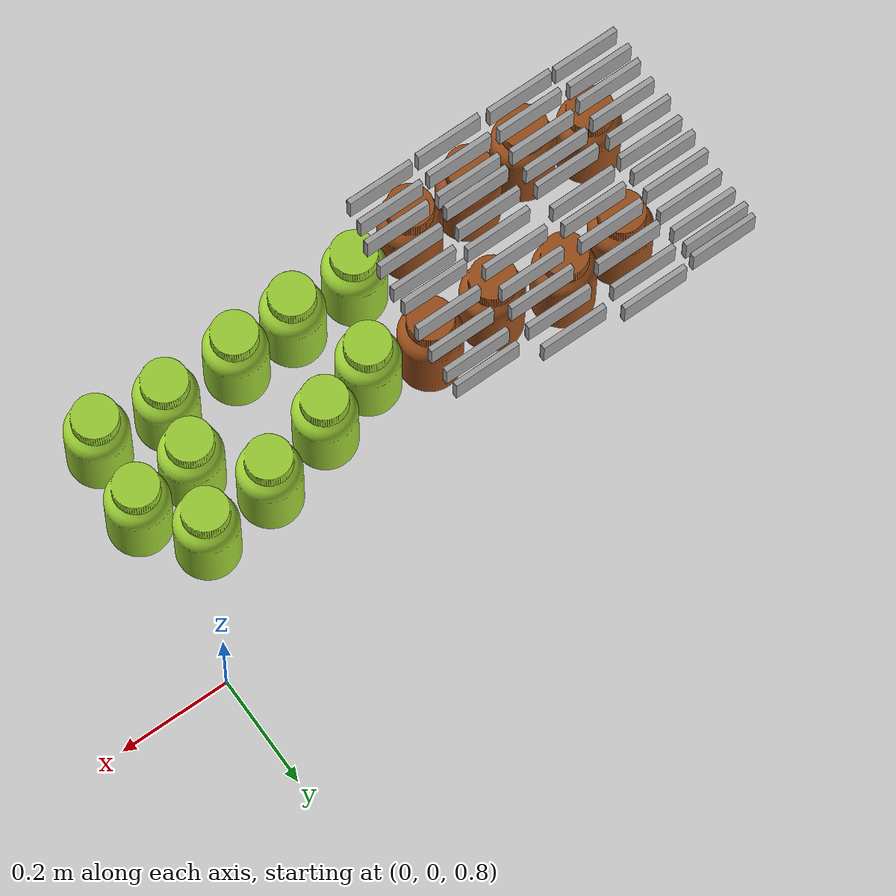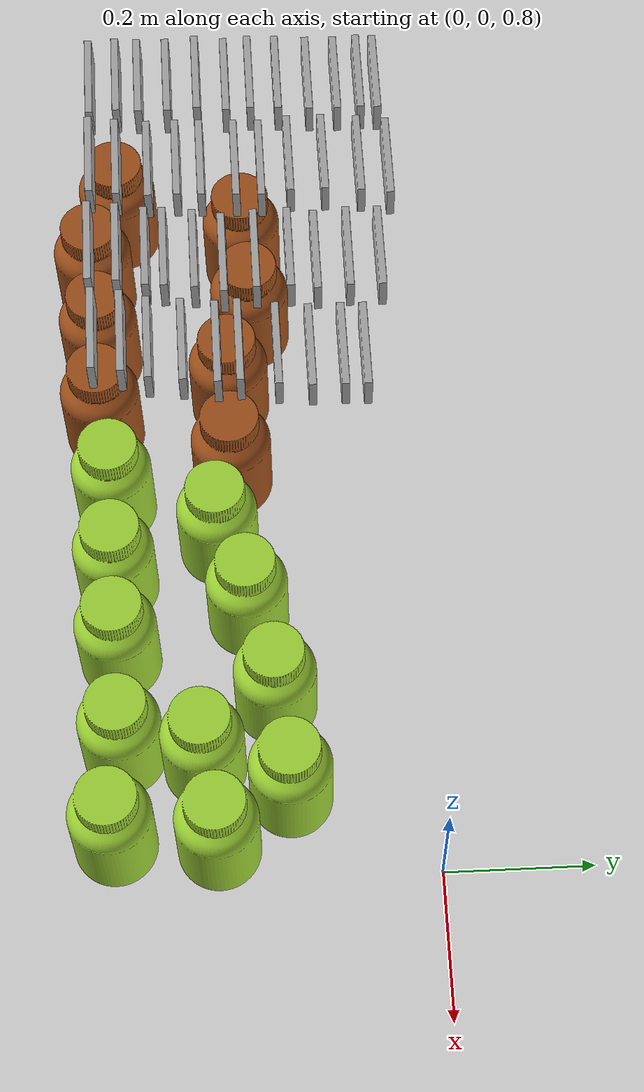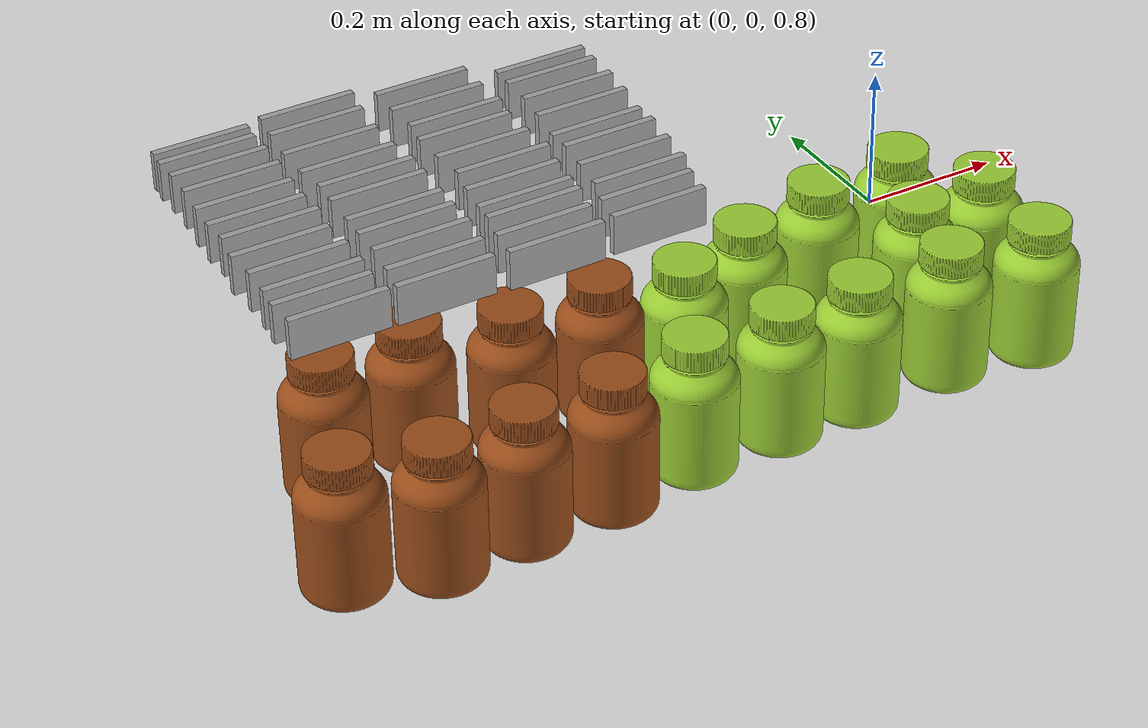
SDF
<sdf version="1.7">
 <world name="default">
  <plugin name="gazebo_ros_factory" filename="libgazebo_ros_factory.so"/>
  <plugin name="attach_detach_plugin" filename="libattach_detach.so"/>
  <gravity>0 0 -9.8</gravity>
  <physics name="default_physics" default="0" type="ode">
   <max_step_size>0.001</max_step_size>
   <real_time_factor>1</real_time_factor>
   <real_time_update_rate>1000</real_time_update_rate>
  </physics>
  <light name="Warehouse_CeilingLight_003" type="point">
   <pose>0 0 9 0 -0 0</pose>
   <diffuse>0.5 0.5 0.5 1</diffuse>
   <specular>0.2 0.2 0.2 1</specular>
   <attenuation>
    <range>80</range>
    <constant>0.3</constant>
    <linear>0.01</linear>
    <quadratic>0.001</quadratic>
   </attenuation>
   <direction>0.1 0.1 -1</direction>
   <spot><inner_angle>0</inner_angle><outer_angle>0</outer_angle><falloff>0</falloff></spot>
  </light>
  <magnetic_field>6e-06 2.3e-05 -4.2e-05</magnetic_field>
  <atmosphere type="adiabatic"/>
  <scene><ambient>0.4 0.4 0.4 1</ambient><background>0.7 0.7 0.7 1</background><shadows>1</shadows></scene>
  <audio><device>default</device></audio>
  <spherical_coordinates>
   <surface_model>EARTH_WGS84</surface_model>
   <latitude_deg>0</latitude_deg>
   <longitude_deg>0</longitude_deg>
   <elevation>0</elevation>
   <heading_deg>0</heading_deg>
  </spherical_coordinates>
  <model name="med_1_0_clone">
   <link name="link_0">
    <inertial>
     <mass>1</mass>
     <inertia>
      <ixx>0.166667</ixx>
      <ixy>0</ixy>
      <ixz>0</ixz>
      <iyy>0.166667</iyy>
      <iyz>0</iyz>
      <izz>0.166667</izz>
     </inertia>
    </inertial>
    <pose>0 -0.005 -0.025 0 -0 0</pose>
    <visual name="visual">
     <pose>0 0.005 0.025 0 -0 0</pose>
     <geometry><mesh><uri>model://med_1/meshes/med-1.dae</uri><scale>0.01 0.01 0.01</scale></mesh></geometry>
     <material>
      <shader type="pixel"><normal_map>__default__</normal_map></shader>
      <emissive>0 0 0 1</emissive>
     </material>
    </visual>
    <collision name="collision">
     <pose>0 0.005 0.025 0 -0 0</pose>
     <geometry><mesh><uri>model://med_1/meshes/med-1.dae</uri><scale>0.01 0.01 0.01</scale></mesh></geometry>
     <surface>
      <friction>
       <ode><mu>1</mu><mu2>1</mu2><fdir1>0 0 0</fdir1><slip1>0</slip1><slip2>0</slip2></ode>
       <torsional>
        <coefficient>1</coefficient>
        <patch_radius>0</patch_radius>
        <surface_radius>0</surface_radius>
        <use_patch_radius>1</use_patch_radius>
        <ode><slip>0</slip></ode>
       </torsional>
      </friction>
      <bounce><restitution_coefficient>0</restitution_coefficient><threshold>1e+06</threshold></bounce>
      <contact>
       <collide_without_contact>0</collide_without_contact>
       <collide_without_contact_bitmask>1</collide_without_contact_bitmask>
       <collide_bitmask>1</collide_bitmask>
       <ode>
        <soft_cfm>0</soft_cfm>
        <soft_erp>0.2</soft_erp>
        <kp>1e+13</kp>
        <kd>1</kd>
        <max_vel>0.01</max_vel>
        <min_depth>0</min_depth>
       </ode>
       <bullet>
        <split_impulse>1</split_impulse>
        <split_impulse_penetration_threshold>-0.01</split_impulse_penetration_threshold>
        <soft_cfm>0</soft_cfm>
        <soft_erp>0.2</soft_erp>
        <kp>1e+13</kp>
        <kd>1</kd>
       </bullet>
      </contact>
     </surface>
    </collision>
   </link>
   <static>0</static>
   <pose>-0.984055 -0.067989 1.20019 -2e-05 0 -3.13179</pose>
  </model>
  <model name="med_1_0_clone_0">
   <link name="link_0">
    <inertial>
     <mass>1</mass>
     <inertia>
      <ixx>0.166667</ixx>
      <ixy>0</ixy>
      <ixz>0</ixz>
      <iyy>0.166667</iyy>
      <iyz>0</iyz>
      <izz>0.166667</izz>
     </inertia>
    </inertial>
    <pose>0 -0.005 -0.025 0 -0 0</pose>
    <visual name="visual">
     <pose>0 0.005 0.025 0 -0 0</pose>
     <geometry><mesh><uri>model://med_1/meshes/med-1.dae</uri><scale>0.01 0.01 0.01</scale></mesh></geometry>
     <material>
      <shader type="pixel"><normal_map>__default__</normal_map></shader>
      <emissive>0 0 0 1</emissive>
     </material>
    </visual>
    <collision name="collision">
     <pose>0 0.005 0.025 0 -0 0</pose>
     <geometry><mesh><uri>model://med_1/meshes/med-1.dae</uri><scale>0.01 0.01 0.01</scale></mesh></geometry>
     <surface>
      <friction>
       <ode><mu>1</mu><mu2>1</mu2><fdir1>0 0 0</fdir1><slip1>0</slip1><slip2>0</slip2></ode>
       <torsional>
        <coefficient>1</coefficient>
        <patch_radius>0</patch_radius>
        <surface_radius>0</surface_radius>
        <use_patch_radius>1</use_patch_radius>
        <ode><slip>0</slip></ode>
       </torsional>
      </friction>
      <bounce><restitution_coefficient>0</restitution_coefficient><threshold>1e+06</threshold></bounce>
      <contact>
       <collide_without_contact>0</collide_without_contact>
       <collide_without_contact_bitmask>1</collide_without_contact_bitmask>
       <collide_bitmask>1</collide_bitmask>
       <ode>
        <soft_cfm>0</soft_cfm>
        <soft_erp>0.2</soft_erp>
        <kp>1e+13</kp>
        <kd>1</kd>
        <max_vel>0.01</max_vel>
        <min_depth>0</min_depth>
       </ode>
       <bullet>
        <split_impulse>1</split_impulse>
        <split_impulse_penetration_threshold>-0.01</split_impulse_penetration_threshold>
        <soft_cfm>0</soft_cfm>
        <soft_erp>0.2</soft_erp>
        <kp>1e+13</kp>
        <kd>1</kd>
       </bullet>
      </contact>
     </surface>
    </collision>
   </link>
   <static>0</static>
   <pose>-0.982142 -0.045704 1.20019 -9e-06 -1e-06 -3.13179</pose>
  </model>
  <model name="med_1_0_clone_1">
   <link name="link_0">
    <inertial>
     <mass>1</mass>
     <inertia>
      <ixx>0.166667</ixx>
      <ixy>0</ixy>
      <ixz>0</ixz>
      <iyy>0.166667</iyy>
      <iyz>0</iyz>
      <izz>0.166667</izz>
     </inertia>
    </inertial>
    <pose>0 -0.005 -0.025 0 -0 0</pose>
    <visual name="visual">
     <pose>0 0.005 0.025 0 -0 0</pose>
     <geometry><mesh><uri>model://med_1/meshes/med-1.dae</uri><scale>0.01 0.01 0.01</scale></mesh></geometry>
     <material>
      <shader type="pixel"><normal_map>__default__</normal_map></shader>
      <emissive>0 0 0 1</emissive>
     </material>
    </visual>
    <collision name="collision">
     <pose>0 0.005 0.025 0 -0 0</pose>
     <geometry><mesh><uri>model://med_1/meshes/med-1.dae</uri><scale>0.01 0.01 0.01</scale></mesh></geometry>
     <surface>
      <friction>
       <ode><mu>1</mu><mu2>1</mu2><fdir1>0 0 0</fdir1><slip1>0</slip1><slip2>0</slip2></ode>
       <torsional>
        <coefficient>1</coefficient>
        <patch_radius>0</patch_radius>
        <surface_radius>0</surface_radius>
        <use_patch_radius>1</use_patch_radius>
        <ode><slip>0</slip></ode>
       </torsional>
      </friction>
      <bounce><restitution_coefficient>0</restitution_coefficient><threshold>1e+06</threshold></bounce>
      <contact>
       <collide_without_contact>0</collide_without_contact>
       <collide_without_contact_bitmask>1</collide_without_contact_bitmask>
       <collide_bitmask>1</collide_bitmask>
       <ode>
        <soft_cfm>0</soft_cfm>
        <soft_erp>0.2</soft_erp>
        <kp>1e+13</kp>
        <kd>1</kd>
        <max_vel>0.01</max_vel>
        <min_depth>0</min_depth>
       </ode>
       <bullet>
        <split_impulse>1</split_impulse>
        <split_impulse_penetration_threshold>-0.01</split_impulse_penetration_threshold>
        <soft_cfm>0</soft_cfm>
        <soft_erp>0.2</soft_erp>
        <kp>1e+13</kp>
        <kd>1</kd>
       </bullet>
      </contact>
     </surface>
    </collision>
   </link>
   <static>0</static>
   <pose>-0.842985 -0.036532 1.20018 -7e-06 -0 -3.1318</pose>
  </model>
  <model name="med_1_0_clone_2">
   <link name="link_0">
    <inertial>
     <mass>1</mass>
     <inertia>
      <ixx>0.166667</ixx>
      <ixy>0</ixy>
      <ixz>0</ixz>
      <iyy>0.166667</iyy>
      <iyz>0</iyz>
      <izz>0.166667</izz>
     </inertia>
    </inertial>
    <pose>0 -0.005 -0.025 0 -0 0</pose>
    <visual name="visual">
     <pose>0 0.005 0.025 0 -0 0</pose>
     <geometry><mesh><uri>model://med_1/meshes/med-1.dae</uri><scale>0.01 0.01 0.01</scale></mesh></geometry>
     <material>
      <shader type="pixel"><normal_map>__default__</normal_map></shader>
      <emissive>0 0 0 1</emissive>
     </material>
    </visual>
    <collision name="collision">
     <pose>0 0.005 0.025 0 -0 0</pose>
     <geometry><mesh><uri>model://med_1/meshes/med-1.dae</uri><scale>0.01 0.01 0.01</scale></mesh></geometry>
     <surface>
      <friction>
       <ode><mu>1</mu><mu2>1</mu2><fdir1>0 0 0</fdir1><slip1>0</slip1><slip2>0</slip2></ode>
       <torsional>
        <coefficient>1</coefficient>
        <patch_radius>0</patch_radius>
        <surface_radius>0</surface_radius>
        <use_patch_radius>1</use_patch_radius>
        <ode><slip>0</slip></ode>
       </torsional>
      </friction>
      <bounce><restitution_coefficient>0</restitution_coefficient><threshold>1e+06</threshold></bounce>
      <contact>
       <collide_without_contact>0</collide_without_contact>
       <collide_without_contact_bitmask>1</collide_without_contact_bitmask>
       <collide_bitmask>1</collide_bitmask>
       <ode>
        <soft_cfm>0</soft_cfm>
        <soft_erp>0.2</soft_erp>
        <kp>1e+13</kp>
        <kd>1</kd>
        <max_vel>0.01</max_vel>
        <min_depth>0</min_depth>
       </ode>
       <bullet>
        <split_impulse>1</split_impulse>
        <split_impulse_penetration_threshold>-0.01</split_impulse_penetration_threshold>
        <soft_cfm>0</soft_cfm>
        <soft_erp>0.2</soft_erp>
        <kp>1e+13</kp>
        <kd>1</kd>
       </bullet>
      </contact>
     </surface>
    </collision>
   </link>
   <static>0</static>
   <pose>-0.555283 -0.151314 1.20018 2e-06 2e-06 -3.1318</pose>
  </model>
  <model name="med_1_0_clone_3">
   <link name="link_0">
    <inertial>
     <mass>1</mass>
     <inertia>
      <ixx>0.166667</ixx>
      <ixy>0</ixy>
      <ixz>0</ixz>
      <iyy>0.166667</iyy>
      <iyz>0</iyz>
      <izz>0.166667</izz>
     </inertia>
    </inertial>
    <pose>0 -0.005 -0.025 0 -0 0</pose>
    <visual name="visual">
     <pose>0 0.005 0.025 0 -0 0</pose>
     <geometry><mesh><uri>model://med_1/meshes/med-1.dae</uri><scale>0.01 0.01 0.01</scale></mesh></geometry>
     <material>
      <shader type="pixel"><normal_map>__default__</normal_map></shader>
      <emissive>0 0 0 1</emissive>
     </material>
    </visual>
    <collision name="collision">
     <pose>0 0.005 0.025 0 -0 0</pose>
     <geometry><mesh><uri>model://med_1/meshes/med-1.dae</uri><scale>0.01 0.01 0.01</scale></mesh></geometry>
     <surface>
      <friction>
       <ode><mu>1</mu><mu2>1</mu2><fdir1>0 0 0</fdir1><slip1>0</slip1><slip2>0</slip2></ode>
       <torsional>
        <coefficient>1</coefficient>
        <patch_radius>0</patch_radius>
        <surface_radius>0</surface_radius>
        <use_patch_radius>1</use_patch_radius>
        <ode><slip>0</slip></ode>
       </torsional>
      </friction>
      <bounce><restitution_coefficient>0</restitution_coefficient><threshold>1e+06</threshold></bounce>
      <contact>
       <collide_without_contact>0</collide_without_contact>
       <collide_without_contact_bitmask>1</collide_without_contact_bitmask>
       <collide_bitmask>1</collide_bitmask>
       <ode>
        <soft_cfm>0</soft_cfm>
        <soft_erp>0.2</soft_erp>
        <kp>1e+13</kp>
        <kd>1</kd>
        <max_vel>0.01</max_vel>
        <min_depth>0</min_depth>
       </ode>
       <bullet>
        <split_impulse>1</split_impulse>
        <split_impulse_penetration_threshold>-0.01</split_impulse_penetration_threshold>
        <soft_cfm>0</soft_cfm>
        <soft_erp>0.2</soft_erp>
        <kp>1e+13</kp>
        <kd>1</kd>
       </bullet>
      </contact>
     </surface>
    </collision>
   </link>
   <static>0</static>
   <pose>-0.701388 -0.054881 1.20018 9e-06 -1e-06 -3.13179</pose>
  </model>
  <model name="med_1_0_clone_4">
   <link name="link_0">
    <inertial>
     <mass>1</mass>
     <inertia>
      <ixx>0.166667</ixx>
      <ixy>0</ixy>
      <ixz>0</ixz>
      <iyy>0.166667</iyy>
      <iyz>0</iyz>
      <izz>0.166667</izz>
     </inertia>
    </inertial>
    <pose>0 -0.005 -0.025 0 -0 0</pose>
    <visual name="visual">
     <pose>0 0.005 0.025 0 -0 0</pose>
     <geometry><mesh><uri>model://med_1/meshes/med-1.dae</uri><scale>0.01 0.01 0.01</scale></mesh></geometry>
     <material>
      <shader type="pixel"><normal_map>__default__</normal_map></shader>
      <emissive>0 0 0 1</emissive>
     </material>
    </visual>
    <collision name="collision">
     <pose>0 0.005 0.025 0 -0 0</pose>
     <geometry><mesh><uri>model://med_1/meshes/med-1.dae</uri><scale>0.01 0.01 0.01</scale></mesh></geometry>
     <surface>
      <friction>
       <ode><mu>1</mu><mu2>1</mu2><fdir1>0 0 0</fdir1><slip1>0</slip1><slip2>0</slip2></ode>
       <torsional>
        <coefficient>1</coefficient>
        <patch_radius>0</patch_radius>
        <surface_radius>0</surface_radius>
        <use_patch_radius>1</use_patch_radius>
        <ode><slip>0</slip></ode>
       </torsional>
      </friction>
      <bounce><restitution_coefficient>0</restitution_coefficient><threshold>1e+06</threshold></bounce>
      <contact>
       <collide_without_contact>0</collide_without_contact>
       <collide_without_contact_bitmask>1</collide_without_contact_bitmask>
       <collide_bitmask>1</collide_bitmask>
       <ode>
        <soft_cfm>0</soft_cfm>
        <soft_erp>0.2</soft_erp>
        <kp>1e+13</kp>
        <kd>1</kd>
        <max_vel>0.01</max_vel>
        <min_depth>0</min_depth>
       </ode>
       <bullet>
        <split_impulse>1</split_impulse>
        <split_impulse_penetration_threshold>-0.01</split_impulse_penetration_threshold>
        <soft_cfm>0</soft_cfm>
        <soft_erp>0.2</soft_erp>
        <kp>1e+13</kp>
        <kd>1</kd>
       </bullet>
      </contact>
     </surface>
    </collision>
   </link>
   <static>0</static>
   <pose>-0.567353 -0.241198 1.20019 -1.7e-05 1e-06 -3.1318</pose>
  </model>
  <model name="med_1_0_clone_5">
   <link name="link_0">
    <inertial>
     <mass>1</mass>
     <inertia>
      <ixx>0.166667</ixx>
      <ixy>0</ixy>
      <ixz>0</ixz>
      <iyy>0.166667</iyy>
      <iyz>0</iyz>
      <izz>0.166667</izz>
     </inertia>
    </inertial>
    <pose>0 -0.005 -0.025 0 -0 0</pose>
    <visual name="visual">
     <pose>0 0.005 0.025 0 -0 0</pose>
     <geometry><mesh><uri>model://med_1/meshes/med-1.dae</uri><scale>0.01 0.01 0.01</scale></mesh></geometry>
     <material>
      <shader type="pixel"><normal_map>__default__</normal_map></shader>
      <emissive>0 0 0 1</emissive>
     </material>
    </visual>
    <collision name="collision">
     <pose>0 0.005 0.025 0 -0 0</pose>
     <geometry><mesh><uri>model://med_1/meshes/med-1.dae</uri><scale>0.01 0.01 0.01</scale></mesh></geometry>
     <surface>
      <friction>
       <ode><mu>1</mu><mu2>1</mu2><fdir1>0 0 0</fdir1><slip1>0</slip1><slip2>0</slip2></ode>
       <torsional>
        <coefficient>1</coefficient>
        <patch_radius>0</patch_radius>
        <surface_radius>0</surface_radius>
        <use_patch_radius>1</use_patch_radius>
        <ode><slip>0</slip></ode>
       </torsional>
      </friction>
      <bounce><restitution_coefficient>0</restitution_coefficient><threshold>1e+06</threshold></bounce>
      <contact>
       <collide_without_contact>0</collide_without_contact>
       <collide_without_contact_bitmask>1</collide_without_contact_bitmask>
       <collide_bitmask>1</collide_bitmask>
       <ode>
        <soft_cfm>0</soft_cfm>
        <soft_erp>0.2</soft_erp>
        <kp>1e+13</kp>
        <kd>1</kd>
        <max_vel>0.01</max_vel>
        <min_depth>0</min_depth>
       </ode>
       <bullet>
        <split_impulse>1</split_impulse>
        <split_impulse_penetration_threshold>-0.01</split_impulse_penetration_threshold>
        <soft_cfm>0</soft_cfm>
        <soft_erp>0.2</soft_erp>
        <kp>1e+13</kp>
        <kd>1</kd>
       </bullet>
      </contact>
     </surface>
    </collision>
   </link>
   <static>0</static>
   <pose>-0.702039 -0.096122 1.20019 -1.2e-05 -1e-06 -3.13738</pose>
  </model>
  <model name="med_1_0_clone_6">
   <link name="link_0">
    <inertial>
     <mass>1</mass>
     <inertia>
      <ixx>0.166667</ixx>
      <ixy>0</ixy>
      <ixz>0</ixz>
      <iyy>0.166667</iyy>
      <iyz>0</iyz>
      <izz>0.166667</izz>
     </inertia>
    </inertial>
    <pose>0 -0.005 -0.025 0 -0 0</pose>
    <visual name="visual">
     <pose>0 0.005 0.025 0 -0 0</pose>
     <geometry><mesh><uri>model://med_1/meshes/med-1.dae</uri><scale>0.01 0.01 0.01</scale></mesh></geometry>
     <material>
      <shader type="pixel"><normal_map>__default__</normal_map></shader>
      <emissive>0 0 0 1</emissive>
     </material>
    </visual>
    <collision name="collision">
     <pose>0 0.005 0.025 0 -0 0</pose>
     <geometry><mesh><uri>model://med_1/meshes/med-1.dae</uri><scale>0.01 0.01 0.01</scale></mesh></geometry>
     <surface>
      <friction>
       <ode><mu>1</mu><mu2>1</mu2><fdir1>0 0 0</fdir1><slip1>0</slip1><slip2>0</slip2></ode>
       <torsional>
        <coefficient>1</coefficient>
        <patch_radius>0</patch_radius>
        <surface_radius>0</surface_radius>
        <use_patch_radius>1</use_patch_radius>
        <ode><slip>0</slip></ode>
       </torsional>
      </friction>
      <bounce><restitution_coefficient>0</restitution_coefficient><threshold>1e+06</threshold></bounce>
      <contact>
       <collide_without_contact>0</collide_without_contact>
       <collide_without_contact_bitmask>1</collide_without_contact_bitmask>
       <collide_bitmask>1</collide_bitmask>
       <ode>
        <soft_cfm>0</soft_cfm>
        <soft_erp>0.2</soft_erp>
        <kp>1e+13</kp>
        <kd>1</kd>
        <max_vel>0.01</max_vel>
        <min_depth>0</min_depth>
       </ode>
       <bullet>
        <split_impulse>1</split_impulse>
        <split_impulse_penetration_threshold>-0.01</split_impulse_penetration_threshold>
        <soft_cfm>0</soft_cfm>
        <soft_erp>0.2</soft_erp>
        <kp>1e+13</kp>
        <kd>1</kd>
       </bullet>
      </contact>
     </surface>
    </collision>
   </link>
   <static>0</static>
   <pose>-0.566184 -0.269641 1.20019 5e-06 -0 -3.13179</pose>
  </model>
  <model name="med_1_0_clone_7">
   <link name="link_0">
    <inertial>
     <mass>1</mass>
     <inertia>
      <ixx>0.166667</ixx>
      <ixy>0</ixy>
      <ixz>0</ixz>
      <iyy>0.166667</iyy>
      <iyz>0</iyz>
      <izz>0.166667</izz>
     </inertia>
    </inertial>
    <pose>0 -0.005 -0.025 0 -0 0</pose>
    <visual name="visual">
     <pose>0 0.005 0.025 0 -0 0</pose>
     <geometry><mesh><uri>model://med_1/meshes/med-1.dae</uri><scale>0.01 0.01 0.01</scale></mesh></geometry>
     <material>
      <shader type="pixel"><normal_map>__default__</normal_map></shader>
      <emissive>0 0 0 1</emissive>
     </material>
    </visual>
    <collision name="collision">
     <pose>0 0.005 0.025 0 -0 0</pose>
     <geometry><mesh><uri>model://med_1/meshes/med-1.dae</uri><scale>0.01 0.01 0.01</scale></mesh></geometry>
     <surface>
      <friction>
       <ode><mu>1</mu><mu2>1</mu2><fdir1>0 0 0</fdir1><slip1>0</slip1><slip2>0</slip2></ode>
       <torsional>
        <coefficient>1</coefficient>
        <patch_radius>0</patch_radius>
        <surface_radius>0</surface_radius>
        <use_patch_radius>1</use_patch_radius>
        <ode><slip>0</slip></ode>
       </torsional>
      </friction>
      <bounce><restitution_coefficient>0</restitution_coefficient><threshold>1e+06</threshold></bounce>
      <contact>
       <collide_without_contact>0</collide_without_contact>
       <collide_without_contact_bitmask>1</collide_without_contact_bitmask>
       <collide_bitmask>1</collide_bitmask>
       <ode>
        <soft_cfm>0</soft_cfm>
        <soft_erp>0.2</soft_erp>
        <kp>1e+13</kp>
        <kd>1</kd>
        <max_vel>0.01</max_vel>
        <min_depth>0</min_depth>
       </ode>
       <bullet>
        <split_impulse>1</split_impulse>
        <split_impulse_penetration_threshold>-0.01</split_impulse_penetration_threshold>
        <soft_cfm>0</soft_cfm>
        <soft_erp>0.2</soft_erp>
        <kp>1e+13</kp>
        <kd>1</kd>
       </bullet>
      </contact>
     </surface>
    </collision>
   </link>
   <static>0</static>
   <pose>-0.700002 -0.258197 1.20018 0 0 -3.13179</pose>
  </model>
  <model name="med_1_0_clone_8">
   <link name="link_0">
    <inertial>
     <mass>1</mass>
     <inertia>
      <ixx>0.166667</ixx>
      <ixy>0</ixy>
      <ixz>0</ixz>
      <iyy>0.166667</iyy>
      <iyz>0</iyz>
      <izz>0.166667</izz>
     </inertia>
    </inertial>
    <pose>0 -0.005 -0.025 0 -0 0</pose>
    <visual name="visual">
     <pose>0 0.005 0.025 0 -0 0</pose>
     <geometry><mesh><uri>model://med_1/meshes/med-1.dae</uri><scale>0.01 0.01 0.01</scale></mesh></geometry>
     <material>
      <shader type="pixel"><normal_map>__default__</normal_map></shader>
      <emissive>0 0 0 1</emissive>
     </material>
    </visual>
    <collision name="collision">
     <pose>0 0.005 0.025 0 -0 0</pose>
     <geometry><mesh><uri>model://med_1/meshes/med-1.dae</uri><scale>0.01 0.01 0.01</scale></mesh></geometry>
     <surface>
      <friction>
       <ode><mu>1</mu><mu2>1</mu2><fdir1>0 0 0</fdir1><slip1>0</slip1><slip2>0</slip2></ode>
       <torsional>
        <coefficient>1</coefficient>
        <patch_radius>0</patch_radius>
        <surface_radius>0</surface_radius>
        <use_patch_radius>1</use_patch_radius>
        <ode><slip>0</slip></ode>
       </torsional>
      </friction>
      <bounce><restitution_coefficient>0</restitution_coefficient><threshold>1e+06</threshold></bounce>
      <contact>
       <collide_without_contact>0</collide_without_contact>
       <collide_without_contact_bitmask>1</collide_without_contact_bitmask>
       <collide_bitmask>1</collide_bitmask>
       <ode>
        <soft_cfm>0</soft_cfm>
        <soft_erp>0.2</soft_erp>
        <kp>1e+13</kp>
        <kd>1</kd>
        <max_vel>0.01</max_vel>
        <min_depth>0</min_depth>
       </ode>
       <bullet>
        <split_impulse>1</split_impulse>
        <split_impulse_penetration_threshold>-0.01</split_impulse_penetration_threshold>
        <soft_cfm>0</soft_cfm>
        <soft_erp>0.2</soft_erp>
        <kp>1e+13</kp>
        <kd>1</kd>
       </bullet>
      </contact>
     </surface>
    </collision>
   </link>
   <static>0</static>
   <pose>-0.84749 -0.204821 1.20019 -2.6e-05 -4e-06 -3.13181</pose>
  </model>
  <model name="med_1_0_clone_9">
   <link name="link_0">
    <inertial>
     <mass>1</mass>
     <inertia>
      <ixx>0.166667</ixx>
      <ixy>0</ixy>
      <ixz>0</ixz>
      <iyy>0.166667</iyy>
      <iyz>0</iyz>
      <izz>0.166667</izz>
     </inertia>
    </inertial>
    <pose>0 -0.005 -0.025 0 -0 0</pose>
    <visual name="visual">
     <pose>0 0.005 0.025 0 -0 0</pose>
     <geometry><mesh><uri>model://med_1/meshes/med-1.dae</uri><scale>0.01 0.01 0.01</scale></mesh></geometry>
     <material>
      <shader type="pixel"><normal_map>__default__</normal_map></shader>
      <emissive>0 0 0 1</emissive>
     </material>
    </visual>
    <collision name="collision">
     <pose>0 0.005 0.025 0 -0 0</pose>
     <geometry><mesh><uri>model://med_1/meshes/med-1.dae</uri><scale>0.01 0.01 0.01</scale></mesh></geometry>
     <surface>
      <friction>
       <ode><mu>1</mu><mu2>1</mu2><fdir1>0 0 0</fdir1><slip1>0</slip1><slip2>0</slip2></ode>
       <torsional>
        <coefficient>1</coefficient>
        <patch_radius>0</patch_radius>
        <surface_radius>0</surface_radius>
        <use_patch_radius>1</use_patch_radius>
        <ode><slip>0</slip></ode>
       </torsional>
      </friction>
      <bounce><restitution_coefficient>0</restitution_coefficient><threshold>1e+06</threshold></bounce>
      <contact>
       <collide_without_contact>0</collide_without_contact>
       <collide_without_contact_bitmask>1</collide_without_contact_bitmask>
       <collide_bitmask>1</collide_bitmask>
       <ode>
        <soft_cfm>0</soft_cfm>
        <soft_erp>0.2</soft_erp>
        <kp>1e+13</kp>
        <kd>1</kd>
        <max_vel>0.01</max_vel>
        <min_depth>0</min_depth>
       </ode>
       <bullet>
        <split_impulse>1</split_impulse>
        <split_impulse_penetration_threshold>-0.01</split_impulse_penetration_threshold>
        <soft_cfm>0</soft_cfm>
        <soft_erp>0.2</soft_erp>
        <kp>1e+13</kp>
        <kd>1</kd>
       </bullet>
      </contact>
     </surface>
    </collision>
   </link>
   <static>0</static>
   <pose>-0.55508 -0.11008 1.20018 -2.5e-05 -1e-06 -3.1318</pose>
  </model>
  <model name="med_1_0_clone_10">
   <link name="link_0">
    <inertial>
     <mass>1</mass>
     <inertia>
      <ixx>0.166667</ixx>
      <ixy>0</ixy>
      <ixz>0</ixz>
      <iyy>0.166667</iyy>
      <iyz>0</iyz>
      <izz>0.166667</izz>
     </inertia>
    </inertial>
    <pose>0 -0.005 -0.025 0 -0 0</pose>
    <visual name="visual">
     <pose>0 0.005 0.025 0 -0 0</pose>
     <geometry><mesh><uri>model://med_1/meshes/med-1.dae</uri><scale>0.01 0.01 0.01</scale></mesh></geometry>
     <material>
      <shader type="pixel"><normal_map>__default__</normal_map></shader>
      <emissive>0 0 0 1</emissive>
     </material>
    </visual>
    <collision name="collision">
     <pose>0 0.005 0.025 0 -0 0</pose>
     <geometry><mesh><uri>model://med_1/meshes/med-1.dae</uri><scale>0.01 0.01 0.01</scale></mesh></geometry>
     <surface>
      <friction>
       <ode><mu>1</mu><mu2>1</mu2><fdir1>0 0 0</fdir1><slip1>0</slip1><slip2>0</slip2></ode>
       <torsional>
        <coefficient>1</coefficient>
        <patch_radius>0</patch_radius>
        <surface_radius>0</surface_radius>
        <use_patch_radius>1</use_patch_radius>
        <ode><slip>0</slip></ode>
       </torsional>
      </friction>
      <bounce><restitution_coefficient>0</restitution_coefficient><threshold>1e+06</threshold></bounce>
      <contact>
       <collide_without_contact>0</collide_without_contact>
       <collide_without_contact_bitmask>1</collide_without_contact_bitmask>
       <collide_bitmask>1</collide_bitmask>
       <ode>
        <soft_cfm>0</soft_cfm>
        <soft_erp>0.2</soft_erp>
        <kp>1e+13</kp>
        <kd>1</kd>
        <max_vel>0.01</max_vel>
        <min_depth>0</min_depth>
       </ode>
       <bullet>
        <split_impulse>1</split_impulse>
        <split_impulse_penetration_threshold>-0.01</split_impulse_penetration_threshold>
        <soft_cfm>0</soft_cfm>
        <soft_erp>0.2</soft_erp>
        <kp>1e+13</kp>
        <kd>1</kd>
       </bullet>
      </contact>
     </surface>
    </collision>
   </link>
   <static>0</static>
   <pose>-0.848659 -0.074496 1.20018 -1.5e-05 -0 -3.13174</pose>
  </model>
  <model name="med_1_0_clone_11">
   <link name="link_0">
    <inertial>
     <mass>1</mass>
     <inertia>
      <ixx>0.166667</ixx>
      <ixy>0</ixy>
      <ixz>0</ixz>
      <iyy>0.166667</iyy>
      <iyz>0</iyz>
      <izz>0.166667</izz>
     </inertia>
    </inertial>
    <pose>0 -0.005 -0.025 0 -0 0</pose>
    <visual name="visual">
     <pose>0 0.005 0.025 0 -0 0</pose>
     <geometry><mesh><uri>model://med_1/meshes/med-1.dae</uri><scale>0.01 0.01 0.01</scale></mesh></geometry>
     <material>
      <shader type="pixel"><normal_map>__default__</normal_map></shader>
      <emissive>0 0 0 1</emissive>
     </material>
    </visual>
    <collision name="collision">
     <pose>0 0.005 0.025 0 -0 0</pose>
     <geometry><mesh><uri>model://med_1/meshes/med-1.dae</uri><scale>0.01 0.01 0.01</scale></mesh></geometry>
     <surface>
      <friction>
       <ode><mu>1</mu><mu2>1</mu2><fdir1>0 0 0</fdir1><slip1>0</slip1><slip2>0</slip2></ode>
       <torsional>
        <coefficient>1</coefficient>
        <patch_radius>0</patch_radius>
        <surface_radius>0</surface_radius>
        <use_patch_radius>1</use_patch_radius>
        <ode><slip>0</slip></ode>
       </torsional>
      </friction>
      <bounce><restitution_coefficient>0</restitution_coefficient><threshold>1e+06</threshold></bounce>
      <contact>
       <collide_without_contact>0</collide_without_contact>
       <collide_without_contact_bitmask>1</collide_without_contact_bitmask>
       <collide_bitmask>1</collide_bitmask>
       <ode>
        <soft_cfm>0</soft_cfm>
        <soft_erp>0.2</soft_erp>
        <kp>1e+13</kp>
        <kd>1</kd>
        <max_vel>0.01</max_vel>
        <min_depth>0</min_depth>
       </ode>
       <bullet>
        <split_impulse>1</split_impulse>
        <split_impulse_penetration_threshold>-0.01</split_impulse_penetration_threshold>
        <soft_cfm>0</soft_cfm>
        <soft_erp>0.2</soft_erp>
        <kp>1e+13</kp>
        <kd>1</kd>
       </bullet>
      </contact>
     </surface>
    </collision>
   </link>
   <static>0</static>
   <pose>-0.85286 -0.16694 1.20019 -2e-06 2e-06 -3.13179</pose>
  </model>
  <model name="med_1_0_clone_12">
   <link name="link_0">
    <inertial>
     <mass>1</mass>
     <inertia>
      <ixx>0.166667</ixx>
      <ixy>0</ixy>
      <ixz>0</ixz>
      <iyy>0.166667</iyy>
      <iyz>0</iyz>
      <izz>0.166667</izz>
     </inertia>
    </inertial>
    <pose>0 -0.005 -0.025 0 -0 0</pose>
    <visual name="visual">
     <pose>0 0.005 0.025 0 -0 0</pose>
     <geometry><mesh><uri>model://med_1/meshes/med-1.dae</uri><scale>0.01 0.01 0.01</scale></mesh></geometry>
     <material>
      <shader type="pixel"><normal_map>__default__</normal_map></shader>
      <emissive>0 0 0 1</emissive>
     </material>
    </visual>
    <collision name="collision">
     <pose>0 0.005 0.025 0 -0 0</pose>
     <geometry><mesh><uri>model://med_1/meshes/med-1.dae</uri><scale>0.01 0.01 0.01</scale></mesh></geometry>
     <surface>
      <friction>
       <ode><mu>1</mu><mu2>1</mu2><fdir1>0 0 0</fdir1><slip1>0</slip1><slip2>0</slip2></ode>
       <torsional>
        <coefficient>1</coefficient>
        <patch_radius>0</patch_radius>
        <surface_radius>0</surface_radius>
        <use_patch_radius>1</use_patch_radius>
        <ode><slip>0</slip></ode>
       </torsional>
      </friction>
      <bounce><restitution_coefficient>0</restitution_coefficient><threshold>1e+06</threshold></bounce>
      <contact>
       <collide_without_contact>0</collide_without_contact>
       <collide_without_contact_bitmask>1</collide_without_contact_bitmask>
       <collide_bitmask>1</collide_bitmask>
       <ode>
        <soft_cfm>0</soft_cfm>
        <soft_erp>0.2</soft_erp>
        <kp>1e+13</kp>
        <kd>1</kd>
        <max_vel>0.01</max_vel>
        <min_depth>0</min_depth>
       </ode>
       <bullet>
        <split_impulse>1</split_impulse>
        <split_impulse_penetration_threshold>-0.01</split_impulse_penetration_threshold>
        <soft_cfm>0</soft_cfm>
        <soft_erp>0.2</soft_erp>
        <kp>1e+13</kp>
        <kd>1</kd>
       </bullet>
      </contact>
     </surface>
    </collision>
   </link>
   <static>0</static>
   <pose>-0.851503 -0.283477 1.20019 -1e-05 -1e-06 -3.1318</pose>
  </model>
  <model name="med_1_0_clone_13">
   <link name="link_0">
    <inertial>
     <mass>1</mass>
     <inertia>
      <ixx>0.166667</ixx>
      <ixy>0</ixy>
      <ixz>0</ixz>
      <iyy>0.166667</iyy>
      <iyz>0</iyz>
      <izz>0.166667</izz>
     </inertia>
    </inertial>
    <pose>0 -0.005 -0.025 0 -0 0</pose>
    <visual name="visual">
     <pose>0 0.005 0.025 0 -0 0</pose>
     <geometry><mesh><uri>model://med_1/meshes/med-1.dae</uri><scale>0.01 0.01 0.01</scale></mesh></geometry>
     <material>
      <shader type="pixel"><normal_map>__default__</normal_map></shader>
      <emissive>0 0 0 1</emissive>
     </material>
    </visual>
    <collision name="collision">
     <pose>0 0.005 0.025 0 -0 0</pose>
     <geometry><mesh><uri>model://med_1/meshes/med-1.dae</uri><scale>0.01 0.01 0.01</scale></mesh></geometry>
     <surface>
      <friction>
       <ode><mu>1</mu><mu2>1</mu2><fdir1>0 0 0</fdir1><slip1>0</slip1><slip2>0</slip2></ode>
       <torsional>
        <coefficient>1</coefficient>
        <patch_radius>0</patch_radius>
        <surface_radius>0</surface_radius>
        <use_patch_radius>1</use_patch_radius>
        <ode><slip>0</slip></ode>
       </torsional>
      </friction>
      <bounce><restitution_coefficient>0</restitution_coefficient><threshold>1e+06</threshold></bounce>
      <contact>
       <collide_without_contact>0</collide_without_contact>
       <collide_without_contact_bitmask>1</collide_without_contact_bitmask>
       <collide_bitmask>1</collide_bitmask>
       <ode>
        <soft_cfm>0</soft_cfm>
        <soft_erp>0.2</soft_erp>
        <kp>1e+13</kp>
        <kd>1</kd>
        <max_vel>0.01</max_vel>
        <min_depth>0</min_depth>
       </ode>
       <bullet>
        <split_impulse>1</split_impulse>
        <split_impulse_penetration_threshold>-0.01</split_impulse_penetration_threshold>
        <soft_cfm>0</soft_cfm>
        <soft_erp>0.2</soft_erp>
        <kp>1e+13</kp>
        <kd>1</kd>
       </bullet>
      </contact>
     </surface>
    </collision>
   </link>
   <static>0</static>
   <pose>-0.704642 -0.17234 1.20019 5e-06 -0 -3.13179</pose>
  </model>
  <model name="med_1_0_clone_14">
   <link name="link_0">
    <inertial>
     <mass>1</mass>
     <inertia>
      <ixx>0.166667</ixx>
      <ixy>0</ixy>
      <ixz>0</ixz>
      <iyy>0.166667</iyy>
      <iyz>0</iyz>
      <izz>0.166667</izz>
     </inertia>
    </inertial>
    <pose>0 -0.005 -0.025 0 -0 0</pose>
    <visual name="visual">
     <pose>0 0.005 0.025 0 -0 0</pose>
     <geometry><mesh><uri>model://med_1/meshes/med-1.dae</uri><scale>0.01 0.01 0.01</scale></mesh></geometry>
     <material>
      <shader type="pixel"><normal_map>__default__</normal_map></shader>
      <emissive>0 0 0 1</emissive>
     </material>
    </visual>
    <collision name="collision">
     <pose>0 0.005 0.025 0 -0 0</pose>
     <geometry><mesh><uri>model://med_1/meshes/med-1.dae</uri><scale>0.01 0.01 0.01</scale></mesh></geometry>
     <surface>
      <friction>
       <ode><mu>1</mu><mu2>1</mu2><fdir1>0 0 0</fdir1><slip1>0</slip1><slip2>0</slip2></ode>
       <torsional>
        <coefficient>1</coefficient>
        <patch_radius>0</patch_radius>
        <surface_radius>0</surface_radius>
        <use_patch_radius>1</use_patch_radius>
        <ode><slip>0</slip></ode>
       </torsional>
      </friction>
      <bounce><restitution_coefficient>0</restitution_coefficient><threshold>1e+06</threshold></bounce>
      <contact>
       <collide_without_contact>0</collide_without_contact>
       <collide_without_contact_bitmask>1</collide_without_contact_bitmask>
       <collide_bitmask>1</collide_bitmask>
       <ode>
        <soft_cfm>0</soft_cfm>
        <soft_erp>0.2</soft_erp>
        <kp>1e+13</kp>
        <kd>1</kd>
        <max_vel>0.01</max_vel>
        <min_depth>0</min_depth>
       </ode>
       <bullet>
        <split_impulse>1</split_impulse>
        <split_impulse_penetration_threshold>-0.01</split_impulse_penetration_threshold>
        <soft_cfm>0</soft_cfm>
        <soft_erp>0.2</soft_erp>
        <kp>1e+13</kp>
        <kd>1</kd>
       </bullet>
      </contact>
     </surface>
    </collision>
   </link>
   <static>0</static>
   <pose>-0.853003 -0.121425 1.20018 -1.1e-05 -1e-06 -3.13179</pose>
  </model>
  <model name="med_1_0_clone_15">
   <link name="link_0">
    <inertial>
     <mass>1</mass>
     <inertia>
      <ixx>0.166667</ixx>
      <ixy>0</ixy>
      <ixz>0</ixz>
      <iyy>0.166667</iyy>
      <iyz>0</iyz>
      <izz>0.166667</izz>
     </inertia>
    </inertial>
    <pose>0 -0.005 -0.025 0 -0 0</pose>
    <visual name="visual">
     <pose>0 0.005 0.025 0 -0 0</pose>
     <geometry><mesh><uri>model://med_1/meshes/med-1.dae</uri><scale>0.01 0.01 0.01</scale></mesh></geometry>
     <material>
      <shader type="pixel"><normal_map>__default__</normal_map></shader>
      <emissive>0 0 0 1</emissive>
     </material>
    </visual>
    <collision name="collision">
     <pose>0 0.005 0.025 0 -0 0</pose>
     <geometry><mesh><uri>model://med_1/meshes/med-1.dae</uri><scale>0.01 0.01 0.01</scale></mesh></geometry>
     <surface>
      <friction>
       <ode><mu>1</mu><mu2>1</mu2><fdir1>0 0 0</fdir1><slip1>0</slip1><slip2>0</slip2></ode>
       <torsional>
        <coefficient>1</coefficient>
        <patch_radius>0</patch_radius>
        <surface_radius>0</surface_radius>
        <use_patch_radius>1</use_patch_radius>
        <ode><slip>0</slip></ode>
       </torsional>
      </friction>
      <bounce><restitution_coefficient>0</restitution_coefficient><threshold>1e+06</threshold></bounce>
      <contact>
       <collide_without_contact>0</collide_without_contact>
       <collide_without_contact_bitmask>1</collide_without_contact_bitmask>
       <collide_bitmask>1</collide_bitmask>
       <ode>
        <soft_cfm>0</soft_cfm>
        <soft_erp>0.2</soft_erp>
        <kp>1e+13</kp>
        <kd>1</kd>
        <max_vel>0.01</max_vel>
        <min_depth>0</min_depth>
       </ode>
       <bullet>
        <split_impulse>1</split_impulse>
        <split_impulse_penetration_threshold>-0.01</split_impulse_penetration_threshold>
        <soft_cfm>0</soft_cfm>
        <soft_erp>0.2</soft_erp>
        <kp>1e+13</kp>
        <kd>1</kd>
       </bullet>
      </contact>
     </surface>
    </collision>
   </link>
   <static>0</static>
   <pose>-0.982692 -0.09912 1.20019 -2e-06 2e-06 -3.13179</pose>
  </model>
  <model name="med_1_0_clone_16">
   <link name="link_0">
    <inertial>
     <mass>1</mass>
     <inertia>
      <ixx>0.166667</ixx>
      <ixy>0</ixy>
      <ixz>0</ixz>
      <iyy>0.166667</iyy>
      <iyz>0</iyz>
      <izz>0.166667</izz>
     </inertia>
    </inertial>
    <pose>0 -0.005 -0.025 0 -0 0</pose>
    <visual name="visual">
     <pose>0 0.005 0.025 0 -0 0</pose>
     <geometry><mesh><uri>model://med_1/meshes/med-1.dae</uri><scale>0.01 0.01 0.01</scale></mesh></geometry>
     <material>
      <shader type="pixel"><normal_map>__default__</normal_map></shader>
      <emissive>0 0 0 1</emissive>
     </material>
    </visual>
    <collision name="collision">
     <pose>0 0.005 0.025 0 -0 0</pose>
     <geometry><mesh><uri>model://med_1/meshes/med-1.dae</uri><scale>0.01 0.01 0.01</scale></mesh></geometry>
     <surface>
      <friction>
       <ode><mu>1</mu><mu2>1</mu2><fdir1>0 0 0</fdir1><slip1>0</slip1><slip2>0</slip2></ode>
       <torsional>
        <coefficient>1</coefficient>
        <patch_radius>0</patch_radius>
        <surface_radius>0</surface_radius>
        <use_patch_radius>1</use_patch_radius>
        <ode><slip>0</slip></ode>
       </torsional>
      </friction>
      <bounce><restitution_coefficient>0</restitution_coefficient><threshold>1e+06</threshold></bounce>
      <contact>
       <collide_without_contact>0</collide_without_contact>
       <collide_without_contact_bitmask>1</collide_without_contact_bitmask>
       <collide_bitmask>1</collide_bitmask>
       <ode>
        <soft_cfm>0</soft_cfm>
        <soft_erp>0.2</soft_erp>
        <kp>1e+13</kp>
        <kd>1</kd>
        <max_vel>0.01</max_vel>
        <min_depth>0</min_depth>
       </ode>
       <bullet>
        <split_impulse>1</split_impulse>
        <split_impulse_penetration_threshold>-0.01</split_impulse_penetration_threshold>
        <soft_cfm>0</soft_cfm>
        <soft_erp>0.2</soft_erp>
        <kp>1e+13</kp>
        <kd>1</kd>
       </bullet>
      </contact>
     </surface>
    </collision>
   </link>
   <static>0</static>
   <pose>-0.986787 -0.24714 1.20018 -1e-06 1e-06 -3.13179</pose>
  </model>
  <model name="med_1_0_clone_17">
   <link name="link_0">
    <inertial>
     <mass>1</mass>
     <inertia>
      <ixx>0.166667</ixx>
      <ixy>0</ixy>
      <ixz>0</ixz>
      <iyy>0.166667</iyy>
      <iyz>0</iyz>
      <izz>0.166667</izz>
     </inertia>
    </inertial>
    <pose>0 -0.005 -0.025 0 -0 0</pose>
    <visual name="visual">
     <pose>0 0.005 0.025 0 -0 0</pose>
     <geometry><mesh><uri>model://med_1/meshes/med-1.dae</uri><scale>0.01 0.01 0.01</scale></mesh></geometry>
     <material>
      <shader type="pixel"><normal_map>__default__</normal_map></shader>
      <emissive>0 0 0 1</emissive>
     </material>
    </visual>
    <collision name="collision">
     <pose>0 0.005 0.025 0 -0 0</pose>
     <geometry><mesh><uri>model://med_1/meshes/med-1.dae</uri><scale>0.01 0.01 0.01</scale></mesh></geometry>
     <surface>
      <friction>
       <ode><mu>1</mu><mu2>1</mu2><fdir1>0 0 0</fdir1><slip1>0</slip1><slip2>0</slip2></ode>
       <torsional>
        <coefficient>1</coefficient>
        <patch_radius>0</patch_radius>
        <surface_radius>0</surface_radius>
        <use_patch_radius>1</use_patch_radius>
        <ode><slip>0</slip></ode>
       </torsional>
      </friction>
      <bounce><restitution_coefficient>0</restitution_coefficient><threshold>1e+06</threshold></bounce>
      <contact>
       <collide_without_contact>0</collide_without_contact>
       <collide_without_contact_bitmask>1</collide_without_contact_bitmask>
       <collide_bitmask>1</collide_bitmask>
       <ode>
        <soft_cfm>0</soft_cfm>
        <soft_erp>0.2</soft_erp>
        <kp>1e+13</kp>
        <kd>1</kd>
        <max_vel>0.01</max_vel>
        <min_depth>0</min_depth>
       </ode>
       <bullet>
        <split_impulse>1</split_impulse>
        <split_impulse_penetration_threshold>-0.01</split_impulse_penetration_threshold>
        <soft_cfm>0</soft_cfm>
        <soft_erp>0.2</soft_erp>
        <kp>1e+13</kp>
        <kd>1</kd>
       </bullet>
      </contact>
     </surface>
    </collision>
   </link>
   <static>0</static>
   <pose>-0.707918 -0.295261 1.20018 8e-06 -1e-06 -3.13178</pose>
  </model>
  <model name="med_1_0_clone_18">
   <link name="link_0">
    <inertial>
     <mass>1</mass>
     <inertia>
      <ixx>0.166667</ixx>
      <ixy>0</ixy>
      <ixz>0</ixz>
      <iyy>0.166667</iyy>
      <iyz>0</iyz>
      <izz>0.166667</izz>
     </inertia>
    </inertial>
    <pose>0 -0.005 -0.025 0 -0 0</pose>
    <visual name="visual">
     <pose>0 0.005 0.025 0 -0 0</pose>
     <geometry><mesh><uri>model://med_1/meshes/med-1.dae</uri><scale>0.01 0.01 0.01</scale></mesh></geometry>
     <material>
      <shader type="pixel"><normal_map>__default__</normal_map></shader>
      <emissive>0 0 0 1</emissive>
     </material>
    </visual>
    <collision name="collision">
     <pose>0 0.005 0.025 0 -0 0</pose>
     <geometry><mesh><uri>model://med_1/meshes/med-1.dae</uri><scale>0.01 0.01 0.01</scale></mesh></geometry>
     <surface>
      <friction>
       <ode><mu>1</mu><mu2>1</mu2><fdir1>0 0 0</fdir1><slip1>0</slip1><slip2>0</slip2></ode>
       <torsional>
        <coefficient>1</coefficient>
        <patch_radius>0</patch_radius>
        <surface_radius>0</surface_radius>
        <use_patch_radius>1</use_patch_radius>
        <ode><slip>0</slip></ode>
       </torsional>
      </friction>
      <bounce><restitution_coefficient>0</restitution_coefficient><threshold>1e+06</threshold></bounce>
      <contact>
       <collide_without_contact>0</collide_without_contact>
       <collide_without_contact_bitmask>1</collide_without_contact_bitmask>
       <collide_bitmask>1</collide_bitmask>
       <ode>
        <soft_cfm>0</soft_cfm>
        <soft_erp>0.2</soft_erp>
        <kp>1e+13</kp>
        <kd>1</kd>
        <max_vel>0.01</max_vel>
        <min_depth>0</min_depth>
       </ode>
       <bullet>
        <split_impulse>1</split_impulse>
        <split_impulse_penetration_threshold>-0.01</split_impulse_penetration_threshold>
        <soft_cfm>0</soft_cfm>
        <soft_erp>0.2</soft_erp>
        <kp>1e+13</kp>
        <kd>1</kd>
       </bullet>
      </contact>
     </surface>
    </collision>
   </link>
   <static>0</static>
   <pose>-0.698931 -0.138289 1.20019 -6e-06 0 -3.13179</pose>
  </model>
  <model name="med_1_0_clone_19">
   <link name="link_0">
    <inertial>
     <mass>1</mass>
     <inertia>
      <ixx>0.166667</ixx>
      <ixy>0</ixy>
      <ixz>0</ixz>
      <iyy>0.166667</iyy>
      <iyz>0</iyz>
      <izz>0.166667</izz>
     </inertia>
    </inertial>
    <pose>0 -0.005 -0.025 0 -0 0</pose>
    <visual name="visual">
     <pose>0 0.005 0.025 0 -0 0</pose>
     <geometry><mesh><uri>model://med_1/meshes/med-1.dae</uri><scale>0.01 0.01 0.01</scale></mesh></geometry>
     <material>
      <shader type="pixel"><normal_map>__default__</normal_map></shader>
      <emissive>0 0 0 1</emissive>
     </material>
    </visual>
    <collision name="collision">
     <pose>0 0.005 0.025 0 -0 0</pose>
     <geometry><mesh><uri>model://med_1/meshes/med-1.dae</uri><scale>0.01 0.01 0.01</scale></mesh></geometry>
     <surface>
      <friction>
       <ode><mu>1</mu><mu2>1</mu2><fdir1>0 0 0</fdir1><slip1>0</slip1><slip2>0</slip2></ode>
       <torsional>
        <coefficient>1</coefficient>
        <patch_radius>0</patch_radius>
        <surface_radius>0</surface_radius>
        <use_patch_radius>1</use_patch_radius>
        <ode><slip>0</slip></ode>
       </torsional>
      </friction>
      <bounce><restitution_coefficient>0</restitution_coefficient><threshold>1e+06</threshold></bounce>
      <contact>
       <collide_without_contact>0</collide_without_contact>
       <collide_without_contact_bitmask>1</collide_without_contact_bitmask>
       <collide_bitmask>1</collide_bitmask>
       <ode>
        <soft_cfm>0</soft_cfm>
        <soft_erp>0.2</soft_erp>
        <kp>1e+13</kp>
        <kd>1</kd>
        <max_vel>0.01</max_vel>
        <min_depth>0</min_depth>
       </ode>
       <bullet>
        <split_impulse>1</split_impulse>
        <split_impulse_penetration_threshold>-0.01</split_impulse_penetration_threshold>
        <soft_cfm>0</soft_cfm>
        <soft_erp>0.2</soft_erp>
        <kp>1e+13</kp>
        <kd>1</kd>
       </bullet>
      </contact>
     </surface>
    </collision>
   </link>
   <static>0</static>
   <pose>-0.987166 -0.177812 1.20019 -2.5e-05 -0 -3.13179</pose>
  </model>
  <model name="med_1_0_clone_20">
   <link name="link_0">
    <inertial>
     <mass>1</mass>
     <inertia>
      <ixx>0.166667</ixx>
      <ixy>0</ixy>
      <ixz>0</ixz>
      <iyy>0.166667</iyy>
      <iyz>0</iyz>
      <izz>0.166667</izz>
     </inertia>
    </inertial>
    <pose>0 -0.005 -0.025 0 -0 0</pose>
    <visual name="visual">
     <pose>0 0.005 0.025 0 -0 0</pose>
     <geometry><mesh><uri>model://med_1/meshes/med-1.dae</uri><scale>0.01 0.01 0.01</scale></mesh></geometry>
     <material>
      <shader type="pixel"><normal_map>__default__</normal_map></shader>
      <emissive>0 0 0 1</emissive>
     </material>
    </visual>
    <collision name="collision">
     <pose>0 0.005 0.025 0 -0 0</pose>
     <geometry><mesh><uri>model://med_1/meshes/med-1.dae</uri><scale>0.01 0.01 0.01</scale></mesh></geometry>
     <surface>
      <friction>
       <ode><mu>1</mu><mu2>1</mu2><fdir1>0 0 0</fdir1><slip1>0</slip1><slip2>0</slip2></ode>
       <torsional>
        <coefficient>1</coefficient>
        <patch_radius>0</patch_radius>
        <surface_radius>0</surface_radius>
        <use_patch_radius>1</use_patch_radius>
        <ode><slip>0</slip></ode>
       </torsional>
      </friction>
      <bounce><restitution_coefficient>0</restitution_coefficient><threshold>1e+06</threshold></bounce>
      <contact>
       <collide_without_contact>0</collide_without_contact>
       <collide_without_contact_bitmask>1</collide_without_contact_bitmask>
       <collide_bitmask>1</collide_bitmask>
       <ode>
        <soft_cfm>0</soft_cfm>
        <soft_erp>0.2</soft_erp>
        <kp>1e+13</kp>
        <kd>1</kd>
        <max_vel>0.01</max_vel>
        <min_depth>0</min_depth>
       </ode>
       <bullet>
        <split_impulse>1</split_impulse>
        <split_impulse_penetration_threshold>-0.01</split_impulse_penetration_threshold>
        <soft_cfm>0</soft_cfm>
        <soft_erp>0.2</soft_erp>
        <kp>1e+13</kp>
        <kd>1</kd>
       </bullet>
      </contact>
     </surface>
    </collision>
   </link>
   <static>0</static>
   <pose>-0.989035 -0.214728 1.20019 -1.4e-05 3e-06 -3.13166</pose>
  </model>
  <model name="med_1_0_clone_21">
   <link name="link_0">
    <inertial>
     <mass>1</mass>
     <inertia>
      <ixx>0.166667</ixx>
      <ixy>0</ixy>
      <ixz>0</ixz>
      <iyy>0.166667</iyy>
      <iyz>0</iyz>
      <izz>0.166667</izz>
     </inertia>
    </inertial>
    <pose>0 -0.005 -0.025 0 -0 0</pose>
    <visual name="visual">
     <pose>0 0.005 0.025 0 -0 0</pose>
     <geometry><mesh><uri>model://med_1/meshes/med-1.dae</uri><scale>0.01 0.01 0.01</scale></mesh></geometry>
     <material>
      <shader type="pixel"><normal_map>__default__</normal_map></shader>
      <emissive>0 0 0 1</emissive>
     </material>
    </visual>
    <collision name="collision">
     <pose>0 0.005 0.025 0 -0 0</pose>
     <geometry><mesh><uri>model://med_1/meshes/med-1.dae</uri><scale>0.01 0.01 0.01</scale></mesh></geometry>
     <surface>
      <friction>
       <ode><mu>1</mu><mu2>1</mu2><fdir1>0 0 0</fdir1><slip1>0</slip1><slip2>0</slip2></ode>
       <torsional>
        <coefficient>1</coefficient>
        <patch_radius>0</patch_radius>
        <surface_radius>0</surface_radius>
        <use_patch_radius>1</use_patch_radius>
        <ode><slip>0</slip></ode>
       </torsional>
      </friction>
      <bounce><restitution_coefficient>0</restitution_coefficient><threshold>1e+06</threshold></bounce>
      <contact>
       <collide_without_contact>0</collide_without_contact>
       <collide_without_contact_bitmask>1</collide_without_contact_bitmask>
       <collide_bitmask>1</collide_bitmask>
       <ode>
        <soft_cfm>0</soft_cfm>
        <soft_erp>0.2</soft_erp>
        <kp>1e+13</kp>
        <kd>1</kd>
        <max_vel>0.01</max_vel>
        <min_depth>0</min_depth>
       </ode>
       <bullet>
        <split_impulse>1</split_impulse>
        <split_impulse_penetration_threshold>-0.01</split_impulse_penetration_threshold>
        <soft_cfm>0</soft_cfm>
        <soft_erp>0.2</soft_erp>
        <kp>1e+13</kp>
        <kd>1</kd>
       </bullet>
      </contact>
     </surface>
    </collision>
   </link>
   <static>0</static>
   <pose>-0.852769 -0.31528 1.20019 -1e-05 0 -3.13178</pose>
  </model>
  <model name="med_1_0_clone_22">
   <link name="link_0">
    <inertial>
     <mass>1</mass>
     <inertia>
      <ixx>0.166667</ixx>
      <ixy>0</ixy>
      <ixz>0</ixz>
      <iyy>0.166667</iyy>
      <iyz>0</iyz>
      <izz>0.166667</izz>
     </inertia>
    </inertial>
    <pose>0 -0.005 -0.025 0 -0 0</pose>
    <visual name="visual">
     <pose>0 0.005 0.025 0 -0 0</pose>
     <geometry><mesh><uri>model://med_1/meshes/med-1.dae</uri><scale>0.01 0.01 0.01</scale></mesh></geometry>
     <material>
      <shader type="pixel"><normal_map>__default__</normal_map></shader>
      <emissive>0 0 0 1</emissive>
     </material>
    </visual>
    <collision name="collision">
     <pose>0 0.005 0.025 0 -0 0</pose>
     <geometry><mesh><uri>model://med_1/meshes/med-1.dae</uri><scale>0.01 0.01 0.01</scale></mesh></geometry>
     <surface>
      <friction>
       <ode><mu>1</mu><mu2>1</mu2><fdir1>0 0 0</fdir1><slip1>0</slip1><slip2>0</slip2></ode>
       <torsional>
        <coefficient>1</coefficient>
        <patch_radius>0</patch_radius>
        <surface_radius>0</surface_radius>
        <use_patch_radius>1</use_patch_radius>
        <ode><slip>0</slip></ode>
       </torsional>
      </friction>
      <bounce><restitution_coefficient>0</restitution_coefficient><threshold>1e+06</threshold></bounce>
      <contact>
       <collide_without_contact>0</collide_without_contact>
       <collide_without_contact_bitmask>1</collide_without_contact_bitmask>
       <collide_bitmask>1</collide_bitmask>
       <ode>
        <soft_cfm>0</soft_cfm>
        <soft_erp>0.2</soft_erp>
        <kp>1e+13</kp>
        <kd>1</kd>
        <max_vel>0.01</max_vel>
        <min_depth>0</min_depth>
       </ode>
       <bullet>
        <split_impulse>1</split_impulse>
        <split_impulse_penetration_threshold>-0.01</split_impulse_penetration_threshold>
        <soft_cfm>0</soft_cfm>
        <soft_erp>0.2</soft_erp>
        <kp>1e+13</kp>
        <kd>1</kd>
       </bullet>
      </contact>
     </surface>
    </collision>
   </link>
   <static>0</static>
   <pose>-0.576751 -0.356544 1.20019 1e-05 -0 -3.13179</pose>
  </model>
  <model name="med_1_0_clone_23">
   <link name="link_0">
    <inertial>
     <mass>1</mass>
     <inertia>
      <ixx>0.166667</ixx>
      <ixy>0</ixy>
      <ixz>0</ixz>
      <iyy>0.166667</iyy>
      <iyz>0</iyz>
      <izz>0.166667</izz>
     </inertia>
    </inertial>
    <pose>0 -0.005 -0.025 0 -0 0</pose>
    <visual name="visual">
     <pose>0 0.005 0.025 0 -0 0</pose>
     <geometry><mesh><uri>model://med_1/meshes/med-1.dae</uri><scale>0.01 0.01 0.01</scale></mesh></geometry>
     <material>
      <shader type="pixel"><normal_map>__default__</normal_map></shader>
      <emissive>0 0 0 1</emissive>
     </material>
    </visual>
    <collision name="collision">
     <pose>0 0.005 0.025 0 -0 0</pose>
     <geometry><mesh><uri>model://med_1/meshes/med-1.dae</uri><scale>0.01 0.01 0.01</scale></mesh></geometry>
     <surface>
      <friction>
       <ode><mu>1</mu><mu2>1</mu2><fdir1>0 0 0</fdir1><slip1>0</slip1><slip2>0</slip2></ode>
       <torsional>
        <coefficient>1</coefficient>
        <patch_radius>0</patch_radius>
        <surface_radius>0</surface_radius>
        <use_patch_radius>1</use_patch_radius>
        <ode><slip>0</slip></ode>
       </torsional>
      </friction>
      <bounce><restitution_coefficient>0</restitution_coefficient><threshold>1e+06</threshold></bounce>
      <contact>
       <collide_without_contact>0</collide_without_contact>
       <collide_without_contact_bitmask>1</collide_without_contact_bitmask>
       <collide_bitmask>1</collide_bitmask>
       <ode>
        <soft_cfm>0</soft_cfm>
        <soft_erp>0.2</soft_erp>
        <kp>1e+13</kp>
        <kd>1</kd>
        <max_vel>0.01</max_vel>
        <min_depth>0</min_depth>
       </ode>
       <bullet>
        <split_impulse>1</split_impulse>
        <split_impulse_penetration_threshold>-0.01</split_impulse_penetration_threshold>
        <soft_cfm>0</soft_cfm>
        <soft_erp>0.2</soft_erp>
        <kp>1e+13</kp>
        <kd>1</kd>
       </bullet>
      </contact>
     </surface>
    </collision>
   </link>
   <static>0</static>
   <pose>-0.983624 -0.136512 1.20018 1e-05 1e-06 -3.13179</pose>
  </model>
  <model name="med_1_0_clone_24">
   <link name="link_0">
    <inertial>
     <mass>1</mass>
     <inertia>
      <ixx>0.166667</ixx>
      <ixy>0</ixy>
      <ixz>0</ixz>
      <iyy>0.166667</iyy>
      <iyz>0</iyz>
      <izz>0.166667</izz>
     </inertia>
    </inertial>
    <pose>0 -0.005 -0.025 0 -0 0</pose>
    <visual name="visual">
     <pose>0 0.005 0.025 0 -0 0</pose>
     <geometry><mesh><uri>model://med_1/meshes/med-1.dae</uri><scale>0.01 0.01 0.01</scale></mesh></geometry>
     <material>
      <shader type="pixel"><normal_map>__default__</normal_map></shader>
      <emissive>0 0 0 1</emissive>
     </material>
    </visual>
    <collision name="collision">
     <pose>0 0.005 0.025 0 -0 0</pose>
     <geometry><mesh><uri>model://med_1/meshes/med-1.dae</uri><scale>0.01 0.01 0.01</scale></mesh></geometry>
     <surface>
      <friction>
       <ode><mu>1</mu><mu2>1</mu2><fdir1>0 0 0</fdir1><slip1>0</slip1><slip2>0</slip2></ode>
       <torsional>
        <coefficient>1</coefficient>
        <patch_radius>0</patch_radius>
        <surface_radius>0</surface_radius>
        <use_patch_radius>1</use_patch_radius>
        <ode><slip>0</slip></ode>
       </torsional>
      </friction>
      <bounce><restitution_coefficient>0</restitution_coefficient><threshold>1e+06</threshold></bounce>
      <contact>
       <collide_without_contact>0</collide_without_contact>
       <collide_without_contact_bitmask>1</collide_without_contact_bitmask>
       <collide_bitmask>1</collide_bitmask>
       <ode>
        <soft_cfm>0</soft_cfm>
        <soft_erp>0.2</soft_erp>
        <kp>1e+13</kp>
        <kd>1</kd>
        <max_vel>0.01</max_vel>
        <min_depth>0</min_depth>
       </ode>
       <bullet>
        <split_impulse>1</split_impulse>
        <split_impulse_penetration_threshold>-0.01</split_impulse_penetration_threshold>
        <soft_cfm>0</soft_cfm>
        <soft_erp>0.2</soft_erp>
        <kp>1e+13</kp>
        <kd>1</kd>
       </bullet>
      </contact>
     </surface>
    </collision>
   </link>
   <static>0</static>
   <pose>-0.849336 -0.237916 1.20019 2e-06 -2e-06 -3.1318</pose>
  </model>
  <model name="med_1_0_clone_25">
   <link name="link_0">
    <inertial>
     <mass>1</mass>
     <inertia>
      <ixx>0.166667</ixx>
      <ixy>0</ixy>
      <ixz>0</ixz>
      <iyy>0.166667</iyy>
      <iyz>0</iyz>
      <izz>0.166667</izz>
     </inertia>
    </inertial>
    <pose>0 -0.005 -0.025 0 -0 0</pose>
    <visual name="visual">
     <pose>0 0.005 0.025 0 -0 0</pose>
     <geometry><mesh><uri>model://med_1/meshes/med-1.dae</uri><scale>0.01 0.01 0.01</scale></mesh></geometry>
     <material>
      <shader type="pixel"><normal_map>__default__</normal_map></shader>
      <emissive>0 0 0 1</emissive>
     </material>
    </visual>
    <collision name="collision">
     <pose>0 0.005 0.025 0 -0 0</pose>
     <geometry><mesh><uri>model://med_1/meshes/med-1.dae</uri><scale>0.01 0.01 0.01</scale></mesh></geometry>
     <surface>
      <friction>
       <ode><mu>1</mu><mu2>1</mu2><fdir1>0 0 0</fdir1><slip1>0</slip1><slip2>0</slip2></ode>
       <torsional>
        <coefficient>1</coefficient>
        <patch_radius>0</patch_radius>
        <surface_radius>0</surface_radius>
        <use_patch_radius>1</use_patch_radius>
        <ode><slip>0</slip></ode>
       </torsional>
      </friction>
      <bounce><restitution_coefficient>0</restitution_coefficient><threshold>1e+06</threshold></bounce>
      <contact>
       <collide_without_contact>0</collide_without_contact>
       <collide_without_contact_bitmask>1</collide_without_contact_bitmask>
       <collide_bitmask>1</collide_bitmask>
       <ode>
        <soft_cfm>0</soft_cfm>
        <soft_erp>0.2</soft_erp>
        <kp>1e+13</kp>
        <kd>1</kd>
        <max_vel>0.01</max_vel>
        <min_depth>0</min_depth>
       </ode>
       <bullet>
        <split_impulse>1</split_impulse>
        <split_impulse_penetration_threshold>-0.01</split_impulse_penetration_threshold>
        <soft_cfm>0</soft_cfm>
        <soft_erp>0.2</soft_erp>
        <kp>1e+13</kp>
        <kd>1</kd>
       </bullet>
      </contact>
     </surface>
    </collision>
   </link>
   <static>0</static>
   <pose>-0.593915 -0.427871 1.20019 -1.3e-05 -0 -3.13179</pose>
  </model>
  <model name="med_1_0_clone_26">
   <link name="link_0">
    <inertial>
     <mass>1</mass>
     <inertia>
      <ixx>0.166667</ixx>
      <ixy>0</ixy>
      <ixz>0</ixz>
      <iyy>0.166667</iyy>
      <iyz>0</iyz>
      <izz>0.166667</izz>
     </inertia>
    </inertial>
    <pose>0 -0.005 -0.025 0 -0 0</pose>
    <visual name="visual">
     <pose>0 0.005 0.025 0 -0 0</pose>
     <geometry><mesh><uri>model://med_1/meshes/med-1.dae</uri><scale>0.01 0.01 0.01</scale></mesh></geometry>
     <material>
      <shader type="pixel"><normal_map>__default__</normal_map></shader>
      <emissive>0 0 0 1</emissive>
     </material>
    </visual>
    <collision name="collision">
     <pose>0 0.005 0.025 0 -0 0</pose>
     <geometry><mesh><uri>model://med_1/meshes/med-1.dae</uri><scale>0.01 0.01 0.01</scale></mesh></geometry>
     <surface>
      <friction>
       <ode><mu>1</mu><mu2>1</mu2><fdir1>0 0 0</fdir1><slip1>0</slip1><slip2>0</slip2></ode>
       <torsional>
        <coefficient>1</coefficient>
        <patch_radius>0</patch_radius>
        <surface_radius>0</surface_radius>
        <use_patch_radius>1</use_patch_radius>
        <ode><slip>0</slip></ode>
       </torsional>
      </friction>
      <bounce><restitution_coefficient>0</restitution_coefficient><threshold>1e+06</threshold></bounce>
      <contact>
       <collide_without_contact>0</collide_without_contact>
       <collide_without_contact_bitmask>1</collide_without_contact_bitmask>
       <collide_bitmask>1</collide_bitmask>
       <ode>
        <soft_cfm>0</soft_cfm>
        <soft_erp>0.2</soft_erp>
        <kp>1e+13</kp>
        <kd>1</kd>
        <max_vel>0.01</max_vel>
        <min_depth>0</min_depth>
       </ode>
       <bullet>
        <split_impulse>1</split_impulse>
        <split_impulse_penetration_threshold>-0.01</split_impulse_penetration_threshold>
        <soft_cfm>0</soft_cfm>
        <soft_erp>0.2</soft_erp>
        <kp>1e+13</kp>
        <kd>1</kd>
       </bullet>
      </contact>
     </surface>
    </collision>
   </link>
   <static>0</static>
   <pose>-0.587979 -0.390916 1.20019 -8e-06 -0 -3.13179</pose>
  </model>
  <model name="med_1_0_clone_27">
   <link name="link_0">
    <inertial>
     <mass>1</mass>
     <inertia>
      <ixx>0.166667</ixx>
      <ixy>0</ixy>
      <ixz>0</ixz>
      <iyy>0.166667</iyy>
      <iyz>0</iyz>
      <izz>0.166667</izz>
     </inertia>
    </inertial>
    <pose>0 -0.005 -0.025 0 -0 0</pose>
    <visual name="visual">
     <pose>0 0.005 0.025 0 -0 0</pose>
     <geometry><mesh><uri>model://med_1/meshes/med-1.dae</uri><scale>0.01 0.01 0.01</scale></mesh></geometry>
     <material>
      <shader type="pixel"><normal_map>__default__</normal_map></shader>
      <emissive>0 0 0 1</emissive>
     </material>
    </visual>
    <collision name="collision">
     <pose>0 0.005 0.025 0 -0 0</pose>
     <geometry><mesh><uri>model://med_1/meshes/med-1.dae</uri><scale>0.01 0.01 0.01</scale></mesh></geometry>
     <surface>
      <friction>
       <ode><mu>1</mu><mu2>1</mu2><fdir1>0 0 0</fdir1><slip1>0</slip1><slip2>0</slip2></ode>
       <torsional>
        <coefficient>1</coefficient>
        <patch_radius>0</patch_radius>
        <surface_radius>0</surface_radius>
        <use_patch_radius>1</use_patch_radius>
        <ode><slip>0</slip></ode>
       </torsional>
      </friction>
      <bounce><restitution_coefficient>0</restitution_coefficient><threshold>1e+06</threshold></bounce>
      <contact>
       <collide_without_contact>0</collide_without_contact>
       <collide_without_contact_bitmask>1</collide_without_contact_bitmask>
       <collide_bitmask>1</collide_bitmask>
       <ode>
        <soft_cfm>0</soft_cfm>
        <soft_erp>0.2</soft_erp>
        <kp>1e+13</kp>
        <kd>1</kd>
        <max_vel>0.01</max_vel>
        <min_depth>0</min_depth>
       </ode>
       <bullet>
        <split_impulse>1</split_impulse>
        <split_impulse_penetration_threshold>-0.01</split_impulse_penetration_threshold>
        <soft_cfm>0</soft_cfm>
        <soft_erp>0.2</soft_erp>
        <kp>1e+13</kp>
        <kd>1</kd>
       </bullet>
      </contact>
     </surface>
    </collision>
   </link>
   <static>0</static>
   <pose>-0.727259 -0.431791 1.20018 -2.1e-05 1e-06 -3.13181</pose>
  </model>
  <model name="med_1_0_clone_28">
   <link name="link_0">
    <inertial>
     <mass>1</mass>
     <inertia>
      <ixx>0.166667</ixx>
      <ixy>0</ixy>
      <ixz>0</ixz>
      <iyy>0.166667</iyy>
      <iyz>0</iyz>
      <izz>0.166667</izz>
     </inertia>
    </inertial>
    <pose>0 -0.005 -0.025 0 -0 0</pose>
    <visual name="visual">
     <pose>0 0.005 0.025 0 -0 0</pose>
     <geometry><mesh><uri>model://med_1/meshes/med-1.dae</uri><scale>0.01 0.01 0.01</scale></mesh></geometry>
     <material>
      <shader type="pixel"><normal_map>__default__</normal_map></shader>
      <emissive>0 0 0 1</emissive>
     </material>
    </visual>
    <collision name="collision">
     <pose>0 0.005 0.025 0 -0 0</pose>
     <geometry><mesh><uri>model://med_1/meshes/med-1.dae</uri><scale>0.01 0.01 0.01</scale></mesh></geometry>
     <surface>
      <friction>
       <ode><mu>1</mu><mu2>1</mu2><fdir1>0 0 0</fdir1><slip1>0</slip1><slip2>0</slip2></ode>
       <torsional>
        <coefficient>1</coefficient>
        <patch_radius>0</patch_radius>
        <surface_radius>0</surface_radius>
        <use_patch_radius>1</use_patch_radius>
        <ode><slip>0</slip></ode>
       </torsional>
      </friction>
      <bounce><restitution_coefficient>0</restitution_coefficient><threshold>1e+06</threshold></bounce>
      <contact>
       <collide_without_contact>0</collide_without_contact>
       <collide_without_contact_bitmask>1</collide_without_contact_bitmask>
       <collide_bitmask>1</collide_bitmask>
       <ode>
        <soft_cfm>0</soft_cfm>
        <soft_erp>0.2</soft_erp>
        <kp>1e+13</kp>
        <kd>1</kd>
        <max_vel>0.01</max_vel>
        <min_depth>0</min_depth>
       </ode>
       <bullet>
        <split_impulse>1</split_impulse>
        <split_impulse_penetration_threshold>-0.01</split_impulse_penetration_threshold>
        <soft_cfm>0</soft_cfm>
        <soft_erp>0.2</soft_erp>
        <kp>1e+13</kp>
        <kd>1</kd>
       </bullet>
      </contact>
     </surface>
    </collision>
   </link>
   <static>0</static>
   <pose>-0.722868 -0.395484 1.20019 -6e-06 0 -3.13178</pose>
  </model>
  <model name="med_1_0_clone_29">
   <link name="link_0">
    <inertial>
     <mass>1</mass>
     <inertia>
      <ixx>0.166667</ixx>
      <ixy>0</ixy>
      <ixz>0</ixz>
      <iyy>0.166667</iyy>
      <iyz>0</iyz>
      <izz>0.166667</izz>
     </inertia>
    </inertial>
    <pose>0 -0.005 -0.025 0 -0 0</pose>
    <visual name="visual">
     <pose>0 0.005 0.025 0 -0 0</pose>
     <geometry><mesh><uri>model://med_1/meshes/med-1.dae</uri><scale>0.01 0.01 0.01</scale></mesh></geometry>
     <material>
      <shader type="pixel"><normal_map>__default__</normal_map></shader>
      <emissive>0 0 0 1</emissive>
     </material>
    </visual>
    <collision name="collision">
     <pose>0 0.005 0.025 0 -0 0</pose>
     <geometry><mesh><uri>model://med_1/meshes/med-1.dae</uri><scale>0.01 0.01 0.01</scale></mesh></geometry>
     <surface>
      <friction>
       <ode><mu>1</mu><mu2>1</mu2><fdir1>0 0 0</fdir1><slip1>0</slip1><slip2>0</slip2></ode>
       <torsional>
        <coefficient>1</coefficient>
        <patch_radius>0</patch_radius>
        <surface_radius>0</surface_radius>
        <use_patch_radius>1</use_patch_radius>
        <ode><slip>0</slip></ode>
       </torsional>
      </friction>
      <bounce><restitution_coefficient>0</restitution_coefficient><threshold>1e+06</threshold></bounce>
      <contact>
       <collide_without_contact>0</collide_without_contact>
       <collide_without_contact_bitmask>1</collide_without_contact_bitmask>
       <collide_bitmask>1</collide_bitmask>
       <ode>
        <soft_cfm>0</soft_cfm>
        <soft_erp>0.2</soft_erp>
        <kp>1e+13</kp>
        <kd>1</kd>
        <max_vel>0.01</max_vel>
        <min_depth>0</min_depth>
       </ode>
       <bullet>
        <split_impulse>1</split_impulse>
        <split_impulse_penetration_threshold>-0.01</split_impulse_penetration_threshold>
        <soft_cfm>0</soft_cfm>
        <soft_erp>0.2</soft_erp>
        <kp>1e+13</kp>
        <kd>1</kd>
       </bullet>
      </contact>
     </surface>
    </collision>
   </link>
   <static>0</static>
   <pose>-0.863893 -0.42989 1.20019 1.3e-05 1e-06 -3.13179</pose>
  </model>
  <model name="med_1_0_clone_30">
   <link name="link_0">
    <inertial>
     <mass>1</mass>
     <inertia>
      <ixx>0.166667</ixx>
      <ixy>0</ixy>
      <ixz>0</ixz>
      <iyy>0.166667</iyy>
      <iyz>0</iyz>
      <izz>0.166667</izz>
     </inertia>
    </inertial>
    <pose>0 -0.005 -0.025 0 -0 0</pose>
    <visual name="visual">
     <pose>0 0.005 0.025 0 -0 0</pose>
     <geometry><mesh><uri>model://med_1/meshes/med-1.dae</uri><scale>0.01 0.01 0.01</scale></mesh></geometry>
     <material>
      <shader type="pixel"><normal_map>__default__</normal_map></shader>
      <emissive>0 0 0 1</emissive>
     </material>
    </visual>
    <collision name="collision">
     <pose>0 0.005 0.025 0 -0 0</pose>
     <geometry><mesh><uri>model://med_1/meshes/med-1.dae</uri><scale>0.01 0.01 0.01</scale></mesh></geometry>
     <surface>
      <friction>
       <ode><mu>1</mu><mu2>1</mu2><fdir1>0 0 0</fdir1><slip1>0</slip1><slip2>0</slip2></ode>
       <torsional>
        <coefficient>1</coefficient>
        <patch_radius>0</patch_radius>
        <surface_radius>0</surface_radius>
        <use_patch_radius>1</use_patch_radius>
        <ode><slip>0</slip></ode>
       </torsional>
      </friction>
      <bounce><restitution_coefficient>0</restitution_coefficient><threshold>1e+06</threshold></bounce>
      <contact>
       <collide_without_contact>0</collide_without_contact>
       <collide_without_contact_bitmask>1</collide_without_contact_bitmask>
       <collide_bitmask>1</collide_bitmask>
       <ode>
        <soft_cfm>0</soft_cfm>
        <soft_erp>0.2</soft_erp>
        <kp>1e+13</kp>
        <kd>1</kd>
        <max_vel>0.01</max_vel>
        <min_depth>0</min_depth>
       </ode>
       <bullet>
        <split_impulse>1</split_impulse>
        <split_impulse_penetration_threshold>-0.01</split_impulse_penetration_threshold>
        <soft_cfm>0</soft_cfm>
        <soft_erp>0.2</soft_erp>
        <kp>1e+13</kp>
        <kd>1</kd>
       </bullet>
      </contact>
     </surface>
    </collision>
   </link>
   <static>0</static>
   <pose>-0.714749 -0.358219 1.20019 1e-05 -1e-06 -3.13178</pose>
  </model>
  <model name="med_1_0_clone_31">
   <link name="link_0">
    <inertial>
     <mass>1</mass>
     <inertia>
      <ixx>0.166667</ixx>
      <ixy>0</ixy>
      <ixz>0</ixz>
      <iyy>0.166667</iyy>
      <iyz>0</iyz>
      <izz>0.166667</izz>
     </inertia>
    </inertial>
    <pose>0 -0.005 -0.025 0 -0 0</pose>
    <visual name="visual">
     <pose>0 0.005 0.025 0 -0 0</pose>
     <geometry><mesh><uri>model://med_1/meshes/med-1.dae</uri><scale>0.01 0.01 0.01</scale></mesh></geometry>
     <material>
      <shader type="pixel"><normal_map>__default__</normal_map></shader>
      <emissive>0 0 0 1</emissive>
     </material>
    </visual>
    <collision name="collision">
     <pose>0 0.005 0.025 0 -0 0</pose>
     <geometry><mesh><uri>model://med_1/meshes/med-1.dae</uri><scale>0.01 0.01 0.01</scale></mesh></geometry>
     <surface>
      <friction>
       <ode><mu>1</mu><mu2>1</mu2><fdir1>0 0 0</fdir1><slip1>0</slip1><slip2>0</slip2></ode>
       <torsional>
        <coefficient>1</coefficient>
        <patch_radius>0</patch_radius>
        <surface_radius>0</surface_radius>
        <use_patch_radius>1</use_patch_radius>
        <ode><slip>0</slip></ode>
       </torsional>
      </friction>
      <bounce><restitution_coefficient>0</restitution_coefficient><threshold>1e+06</threshold></bounce>
      <contact>
       <collide_without_contact>0</collide_without_contact>
       <collide_without_contact_bitmask>1</collide_without_contact_bitmask>
       <collide_bitmask>1</collide_bitmask>
       <ode>
        <soft_cfm>0</soft_cfm>
        <soft_erp>0.2</soft_erp>
        <kp>1e+13</kp>
        <kd>1</kd>
        <max_vel>0.01</max_vel>
        <min_depth>0</min_depth>
       </ode>
       <bullet>
        <split_impulse>1</split_impulse>
        <split_impulse_penetration_threshold>-0.01</split_impulse_penetration_threshold>
        <soft_cfm>0</soft_cfm>
        <soft_erp>0.2</soft_erp>
        <kp>1e+13</kp>
        <kd>1</kd>
       </bullet>
      </contact>
     </surface>
    </collision>
   </link>
   <static>0</static>
   <pose>-0.989511 -0.325607 1.20019 -1.9e-05 0 -3.13178</pose>
  </model>
  <model name="med_1_0_clone_32">
   <link name="link_0">
    <inertial>
     <mass>1</mass>
     <inertia>
      <ixx>0.166667</ixx>
      <ixy>0</ixy>
      <ixz>0</ixz>
      <iyy>0.166667</iyy>
      <iyz>0</iyz>
      <izz>0.166667</izz>
     </inertia>
    </inertial>
    <pose>0 -0.005 -0.025 0 -0 0</pose>
    <visual name="visual">
     <pose>0 0.005 0.025 0 -0 0</pose>
     <geometry><mesh><uri>model://med_1/meshes/med-1.dae</uri><scale>0.01 0.01 0.01</scale></mesh></geometry>
     <material>
      <shader type="pixel"><normal_map>__default__</normal_map></shader>
      <emissive>0 0 0 1</emissive>
     </material>
    </visual>
    <collision name="collision">
     <pose>0 0.005 0.025 0 -0 0</pose>
     <geometry><mesh><uri>model://med_1/meshes/med-1.dae</uri><scale>0.01 0.01 0.01</scale></mesh></geometry>
     <surface>
      <friction>
       <ode><mu>1</mu><mu2>1</mu2><fdir1>0 0 0</fdir1><slip1>0</slip1><slip2>0</slip2></ode>
       <torsional>
        <coefficient>1</coefficient>
        <patch_radius>0</patch_radius>
        <surface_radius>0</surface_radius>
        <use_patch_radius>1</use_patch_radius>
        <ode><slip>0</slip></ode>
       </torsional>
      </friction>
      <bounce><restitution_coefficient>0</restitution_coefficient><threshold>1e+06</threshold></bounce>
      <contact>
       <collide_without_contact>0</collide_without_contact>
       <collide_without_contact_bitmask>1</collide_without_contact_bitmask>
       <collide_bitmask>1</collide_bitmask>
       <ode>
        <soft_cfm>0</soft_cfm>
        <soft_erp>0.2</soft_erp>
        <kp>1e+13</kp>
        <kd>1</kd>
        <max_vel>0.01</max_vel>
        <min_depth>0</min_depth>
       </ode>
       <bullet>
        <split_impulse>1</split_impulse>
        <split_impulse_penetration_threshold>-0.01</split_impulse_penetration_threshold>
        <soft_cfm>0</soft_cfm>
        <soft_erp>0.2</soft_erp>
        <kp>1e+13</kp>
        <kd>1</kd>
       </bullet>
      </contact>
     </surface>
    </collision>
   </link>
   <static>0</static>
   <pose>-0.712807 -0.334258 1.20019 0 -1e-06 -3.13178</pose>
  </model>
  <model name="med_1_0_clone_33">
   <link name="link_0">
    <inertial>
     <mass>1</mass>
     <inertia>
      <ixx>0.166667</ixx>
      <ixy>0</ixy>
      <ixz>0</ixz>
      <iyy>0.166667</iyy>
      <iyz>0</iyz>
      <izz>0.166667</izz>
     </inertia>
    </inertial>
    <pose>0 -0.005 -0.025 0 -0 0</pose>
    <visual name="visual">
     <pose>0 0.005 0.025 0 -0 0</pose>
     <geometry><mesh><uri>model://med_1/meshes/med-1.dae</uri><scale>0.01 0.01 0.01</scale></mesh></geometry>
     <material>
      <shader type="pixel"><normal_map>__default__</normal_map></shader>
      <emissive>0 0 0 1</emissive>
     </material>
    </visual>
    <collision name="collision">
     <pose>0 0.005 0.025 0 -0 0</pose>
     <geometry><mesh><uri>model://med_1/meshes/med-1.dae</uri><scale>0.01 0.01 0.01</scale></mesh></geometry>
     <surface>
      <friction>
       <ode><mu>1</mu><mu2>1</mu2><fdir1>0 0 0</fdir1><slip1>0</slip1><slip2>0</slip2></ode>
       <torsional>
        <coefficient>1</coefficient>
        <patch_radius>0</patch_radius>
        <surface_radius>0</surface_radius>
        <use_patch_radius>1</use_patch_radius>
        <ode><slip>0</slip></ode>
       </torsional>
      </friction>
      <bounce><restitution_coefficient>0</restitution_coefficient><threshold>1e+06</threshold></bounce>
      <contact>
       <collide_without_contact>0</collide_without_contact>
       <collide_without_contact_bitmask>1</collide_without_contact_bitmask>
       <collide_bitmask>1</collide_bitmask>
       <ode>
        <soft_cfm>0</soft_cfm>
        <soft_erp>0.2</soft_erp>
        <kp>1e+13</kp>
        <kd>1</kd>
        <max_vel>0.01</max_vel>
        <min_depth>0</min_depth>
       </ode>
       <bullet>
        <split_impulse>1</split_impulse>
        <split_impulse_penetration_threshold>-0.01</split_impulse_penetration_threshold>
        <soft_cfm>0</soft_cfm>
        <soft_erp>0.2</soft_erp>
        <kp>1e+13</kp>
        <kd>1</kd>
       </bullet>
      </contact>
     </surface>
    </collision>
   </link>
   <static>0</static>
   <pose>-0.990541 -0.364091 1.20019 -5e-06 -0 -3.13178</pose>
  </model>
  <model name="med_1_0_clone_34">
   <link name="link_0">
    <inertial>
     <mass>1</mass>
     <inertia>
      <ixx>0.166667</ixx>
      <ixy>0</ixy>
      <ixz>0</ixz>
      <iyy>0.166667</iyy>
      <iyz>0</iyz>
      <izz>0.166667</izz>
     </inertia>
    </inertial>
    <pose>0 -0.005 -0.025 0 -0 0</pose>
    <visual name="visual">
     <pose>0 0.005 0.025 0 -0 0</pose>
     <geometry><mesh><uri>model://med_1/meshes/med-1.dae</uri><scale>0.01 0.01 0.01</scale></mesh></geometry>
     <material>
      <shader type="pixel"><normal_map>__default__</normal_map></shader>
      <emissive>0 0 0 1</emissive>
     </material>
    </visual>
    <collision name="collision">
     <pose>0 0.005 0.025 0 -0 0</pose>
     <geometry><mesh><uri>model://med_1/meshes/med-1.dae</uri><scale>0.01 0.01 0.01</scale></mesh></geometry>
     <surface>
      <friction>
       <ode><mu>1</mu><mu2>1</mu2><fdir1>0 0 0</fdir1><slip1>0</slip1><slip2>0</slip2></ode>
       <torsional>
        <coefficient>1</coefficient>
        <patch_radius>0</patch_radius>
        <surface_radius>0</surface_radius>
        <use_patch_radius>1</use_patch_radius>
        <ode><slip>0</slip></ode>
       </torsional>
      </friction>
      <bounce><restitution_coefficient>0</restitution_coefficient><threshold>1e+06</threshold></bounce>
      <contact>
       <collide_without_contact>0</collide_without_contact>
       <collide_without_contact_bitmask>1</collide_without_contact_bitmask>
       <collide_bitmask>1</collide_bitmask>
       <ode>
        <soft_cfm>0</soft_cfm>
        <soft_erp>0.2</soft_erp>
        <kp>1e+13</kp>
        <kd>1</kd>
        <max_vel>0.01</max_vel>
        <min_depth>0</min_depth>
       </ode>
       <bullet>
        <split_impulse>1</split_impulse>
        <split_impulse_penetration_threshold>-0.01</split_impulse_penetration_threshold>
        <soft_cfm>0</soft_cfm>
        <soft_erp>0.2</soft_erp>
        <kp>1e+13</kp>
        <kd>1</kd>
       </bullet>
      </contact>
     </surface>
    </collision>
   </link>
   <static>0</static>
   <pose>-0.571396 -0.313119 1.20019 5e-06 -0 -3.13178</pose>
  </model>
  <model name="med_1_0_clone_35">
   <link name="link_0">
    <inertial>
     <mass>1</mass>
     <inertia>
      <ixx>0.166667</ixx>
      <ixy>0</ixy>
      <ixz>0</ixz>
      <iyy>0.166667</iyy>
      <iyz>0</iyz>
      <izz>0.166667</izz>
     </inertia>
    </inertial>
    <pose>0 -0.005 -0.025 0 -0 0</pose>
    <visual name="visual">
     <pose>0 0.005 0.025 0 -0 0</pose>
     <geometry><mesh><uri>model://med_1/meshes/med-1.dae</uri><scale>0.01 0.01 0.01</scale></mesh></geometry>
     <material>
      <shader type="pixel"><normal_map>__default__</normal_map></shader>
      <emissive>0 0 0 1</emissive>
     </material>
    </visual>
    <collision name="collision">
     <pose>0 0.005 0.025 0 -0 0</pose>
     <geometry><mesh><uri>model://med_1/meshes/med-1.dae</uri><scale>0.01 0.01 0.01</scale></mesh></geometry>
     <surface>
      <friction>
       <ode><mu>1</mu><mu2>1</mu2><fdir1>0 0 0</fdir1><slip1>0</slip1><slip2>0</slip2></ode>
       <torsional>
        <coefficient>1</coefficient>
        <patch_radius>0</patch_radius>
        <surface_radius>0</surface_radius>
        <use_patch_radius>1</use_patch_radius>
        <ode><slip>0</slip></ode>
       </torsional>
      </friction>
      <bounce><restitution_coefficient>0</restitution_coefficient><threshold>1e+06</threshold></bounce>
      <contact>
       <collide_without_contact>0</collide_without_contact>
       <collide_without_contact_bitmask>1</collide_without_contact_bitmask>
       <collide_bitmask>1</collide_bitmask>
       <ode>
        <soft_cfm>0</soft_cfm>
        <soft_erp>0.2</soft_erp>
        <kp>1e+13</kp>
        <kd>1</kd>
        <max_vel>0.01</max_vel>
        <min_depth>0</min_depth>
       </ode>
       <bullet>
        <split_impulse>1</split_impulse>
        <split_impulse_penetration_threshold>-0.01</split_impulse_penetration_threshold>
        <soft_cfm>0</soft_cfm>
        <soft_erp>0.2</soft_erp>
        <kp>1e+13</kp>
        <kd>1</kd>
       </bullet>
      </contact>
     </surface>
    </collision>
   </link>
   <static>0</static>
   <pose>-0.858212 -0.394664 1.20018 -3e-06 -0 -3.13178</pose>
  </model>
  <model name="med_1_0_clone_36">
   <link name="link_0">
    <inertial>
     <mass>1</mass>
     <inertia>
      <ixx>0.166667</ixx>
      <ixy>0</ixy>
      <ixz>0</ixz>
      <iyy>0.166667</iyy>
      <iyz>0</iyz>
      <izz>0.166667</izz>
     </inertia>
    </inertial>
    <pose>0 -0.005 -0.025 0 -0 0</pose>
    <visual name="visual">
     <pose>0 0.005 0.025 0 -0 0</pose>
     <geometry><mesh><uri>model://med_1/meshes/med-1.dae</uri><scale>0.01 0.01 0.01</scale></mesh></geometry>
     <material>
      <shader type="pixel"><normal_map>__default__</normal_map></shader>
      <emissive>0 0 0 1</emissive>
     </material>
    </visual>
    <collision name="collision">
     <pose>0 0.005 0.025 0 -0 0</pose>
     <geometry><mesh><uri>model://med_1/meshes/med-1.dae</uri><scale>0.01 0.01 0.01</scale></mesh></geometry>
     <surface>
      <friction>
       <ode><mu>1</mu><mu2>1</mu2><fdir1>0 0 0</fdir1><slip1>0</slip1><slip2>0</slip2></ode>
       <torsional>
        <coefficient>1</coefficient>
        <patch_radius>0</patch_radius>
        <surface_radius>0</surface_radius>
        <use_patch_radius>1</use_patch_radius>
        <ode><slip>0</slip></ode>
       </torsional>
      </friction>
      <bounce><restitution_coefficient>0</restitution_coefficient><threshold>1e+06</threshold></bounce>
      <contact>
       <collide_without_contact>0</collide_without_contact>
       <collide_without_contact_bitmask>1</collide_without_contact_bitmask>
       <collide_bitmask>1</collide_bitmask>
       <ode>
        <soft_cfm>0</soft_cfm>
        <soft_erp>0.2</soft_erp>
        <kp>1e+13</kp>
        <kd>1</kd>
        <max_vel>0.01</max_vel>
        <min_depth>0</min_depth>
       </ode>
       <bullet>
        <split_impulse>1</split_impulse>
        <split_impulse_penetration_threshold>-0.01</split_impulse_penetration_threshold>
        <soft_cfm>0</soft_cfm>
        <soft_erp>0.2</soft_erp>
        <kp>1e+13</kp>
        <kd>1</kd>
       </bullet>
      </contact>
     </surface>
    </collision>
   </link>
   <static>0</static>
   <pose>-0.852914 -0.353013 1.20019 -1.5e-05 -2e-06 -3.13178</pose>
  </model>
  <model name="med_1_0_clone_37">
   <link name="link_0">
    <inertial>
     <mass>1</mass>
     <inertia>
      <ixx>0.166667</ixx>
      <ixy>0</ixy>
      <ixz>0</ixz>
      <iyy>0.166667</iyy>
      <iyz>0</iyz>
      <izz>0.166667</izz>
     </inertia>
    </inertial>
    <pose>0 -0.005 -0.025 0 -0 0</pose>
    <visual name="visual">
     <pose>0 0.005 0.025 0 -0 0</pose>
     <geometry><mesh><uri>model://med_1/meshes/med-1.dae</uri><scale>0.01 0.01 0.01</scale></mesh></geometry>
     <material>
      <shader type="pixel"><normal_map>__default__</normal_map></shader>
      <emissive>0 0 0 1</emissive>
     </material>
    </visual>
    <collision name="collision">
     <pose>0 0.005 0.025 0 -0 0</pose>
     <geometry><mesh><uri>model://med_1/meshes/med-1.dae</uri><scale>0.01 0.01 0.01</scale></mesh></geometry>
     <surface>
      <friction>
       <ode><mu>1</mu><mu2>1</mu2><fdir1>0 0 0</fdir1><slip1>0</slip1><slip2>0</slip2></ode>
       <torsional>
        <coefficient>1</coefficient>
        <patch_radius>0</patch_radius>
        <surface_radius>0</surface_radius>
        <use_patch_radius>1</use_patch_radius>
        <ode><slip>0</slip></ode>
       </torsional>
      </friction>
      <bounce><restitution_coefficient>0</restitution_coefficient><threshold>1e+06</threshold></bounce>
      <contact>
       <collide_without_contact>0</collide_without_contact>
       <collide_without_contact_bitmask>1</collide_without_contact_bitmask>
       <collide_bitmask>1</collide_bitmask>
       <ode>
        <soft_cfm>0</soft_cfm>
        <soft_erp>0.2</soft_erp>
        <kp>1e+13</kp>
        <kd>1</kd>
        <max_vel>0.01</max_vel>
        <min_depth>0</min_depth>
       </ode>
       <bullet>
        <split_impulse>1</split_impulse>
        <split_impulse_penetration_threshold>-0.01</split_impulse_penetration_threshold>
        <soft_cfm>0</soft_cfm>
        <soft_erp>0.2</soft_erp>
        <kp>1e+13</kp>
        <kd>1</kd>
       </bullet>
      </contact>
     </surface>
    </collision>
   </link>
   <static>0</static>
   <pose>-0.559642 -0.193357 1.20018 -9e-06 -1e-06 -3.13179</pose>
  </model>
  <model name="med_1_0_clone_38">
   <link name="link_0">
    <inertial>
     <mass>1</mass>
     <inertia>
      <ixx>0.166667</ixx>
      <ixy>0</ixy>
      <ixz>0</ixz>
      <iyy>0.166667</iyy>
      <iyz>0</iyz>
      <izz>0.166667</izz>
     </inertia>
    </inertial>
    <pose>0 -0.005 -0.025 0 -0 0</pose>
    <visual name="visual">
     <pose>0 0.005 0.025 0 -0 0</pose>
     <geometry><mesh><uri>model://med_1/meshes/med-1.dae</uri><scale>0.01 0.01 0.01</scale></mesh></geometry>
     <material>
      <shader type="pixel"><normal_map>__default__</normal_map></shader>
      <emissive>0 0 0 1</emissive>
     </material>
    </visual>
    <collision name="collision">
     <pose>0 0.005 0.025 0 -0 0</pose>
     <geometry><mesh><uri>model://med_1/meshes/med-1.dae</uri><scale>0.01 0.01 0.01</scale></mesh></geometry>
     <surface>
      <friction>
       <ode><mu>1</mu><mu2>1</mu2><fdir1>0 0 0</fdir1><slip1>0</slip1><slip2>0</slip2></ode>
       <torsional>
        <coefficient>1</coefficient>
        <patch_radius>0</patch_radius>
        <surface_radius>0</surface_radius>
        <use_patch_radius>1</use_patch_radius>
        <ode><slip>0</slip></ode>
       </torsional>
      </friction>
      <bounce><restitution_coefficient>0</restitution_coefficient><threshold>1e+06</threshold></bounce>
      <contact>
       <collide_without_contact>0</collide_without_contact>
       <collide_without_contact_bitmask>1</collide_without_contact_bitmask>
       <collide_bitmask>1</collide_bitmask>
       <ode>
        <soft_cfm>0</soft_cfm>
        <soft_erp>0.2</soft_erp>
        <kp>1e+13</kp>
        <kd>1</kd>
        <max_vel>0.01</max_vel>
        <min_depth>0</min_depth>
       </ode>
       <bullet>
        <split_impulse>1</split_impulse>
        <split_impulse_penetration_threshold>-0.01</split_impulse_penetration_threshold>
        <soft_cfm>0</soft_cfm>
        <soft_erp>0.2</soft_erp>
        <kp>1e+13</kp>
        <kd>1</kd>
       </bullet>
      </contact>
     </surface>
    </collision>
   </link>
   <static>0</static>
   <pose>-0.704229 -0.21626 1.20019 -3e-06 2e-06 -3.13179</pose>
  </model>
  <model name="med_1_0_clone_39">
   <link name="link_0">
    <inertial>
     <mass>1</mass>
     <inertia>
      <ixx>0.166667</ixx>
      <ixy>0</ixy>
      <ixz>0</ixz>
      <iyy>0.166667</iyy>
      <iyz>0</iyz>
      <izz>0.166667</izz>
     </inertia>
    </inertial>
    <pose>0 -0.005 -0.025 0 -0 0</pose>
    <visual name="visual">
     <pose>0 0.005 0.025 0 -0 0</pose>
     <geometry><mesh><uri>model://med_1/meshes/med-1.dae</uri><scale>0.01 0.01 0.01</scale></mesh></geometry>
     <material>
      <shader type="pixel"><normal_map>__default__</normal_map></shader>
      <emissive>0 0 0 1</emissive>
     </material>
    </visual>
    <collision name="collision">
     <pose>0 0.005 0.025 0 -0 0</pose>
     <geometry><mesh><uri>model://med_1/meshes/med-1.dae</uri><scale>0.01 0.01 0.01</scale></mesh></geometry>
     <surface>
      <friction>
       <ode><mu>1</mu><mu2>1</mu2><fdir1>0 0 0</fdir1><slip1>0</slip1><slip2>0</slip2></ode>
       <torsional>
        <coefficient>1</coefficient>
        <patch_radius>0</patch_radius>
        <surface_radius>0</surface_radius>
        <use_patch_radius>1</use_patch_radius>
        <ode><slip>0</slip></ode>
       </torsional>
      </friction>
      <bounce><restitution_coefficient>0</restitution_coefficient><threshold>1e+06</threshold></bounce>
      <contact>
       <collide_without_contact>0</collide_without_contact>
       <collide_without_contact_bitmask>1</collide_without_contact_bitmask>
       <collide_bitmask>1</collide_bitmask>
       <ode>
        <soft_cfm>0</soft_cfm>
        <soft_erp>0.2</soft_erp>
        <kp>1e+13</kp>
        <kd>1</kd>
        <max_vel>0.01</max_vel>
        <min_depth>0</min_depth>
       </ode>
       <bullet>
        <split_impulse>1</split_impulse>
        <split_impulse_penetration_threshold>-0.01</split_impulse_penetration_threshold>
        <soft_cfm>0</soft_cfm>
        <soft_erp>0.2</soft_erp>
        <kp>1e+13</kp>
        <kd>1</kd>
       </bullet>
      </contact>
     </surface>
    </collision>
   </link>
   <static>0</static>
   <pose>-0.993438 -0.393533 1.20019 -2e-06 -0 -3.13178</pose>
  </model>
  <model name="med_1_0_clone_40">
   <link name="link_0">
    <inertial>
     <mass>1</mass>
     <inertia>
      <ixx>0.166667</ixx>
      <ixy>0</ixy>
      <ixz>0</ixz>
      <iyy>0.166667</iyy>
      <iyz>0</iyz>
      <izz>0.166667</izz>
     </inertia>
    </inertial>
    <pose>0 -0.005 -0.025 0 -0 0</pose>
    <visual name="visual">
     <pose>0 0.005 0.025 0 -0 0</pose>
     <geometry><mesh><uri>model://med_1/meshes/med-1.dae</uri><scale>0.01 0.01 0.01</scale></mesh></geometry>
     <material>
      <shader type="pixel"><normal_map>__default__</normal_map></shader>
      <emissive>0 0 0 1</emissive>
     </material>
    </visual>
    <collision name="collision">
     <pose>0 0.005 0.025 0 -0 0</pose>
     <geometry><mesh><uri>model://med_1/meshes/med-1.dae</uri><scale>0.01 0.01 0.01</scale></mesh></geometry>
     <surface>
      <friction>
       <ode><mu>1</mu><mu2>1</mu2><fdir1>0 0 0</fdir1><slip1>0</slip1><slip2>0</slip2></ode>
       <torsional>
        <coefficient>1</coefficient>
        <patch_radius>0</patch_radius>
        <surface_radius>0</surface_radius>
        <use_patch_radius>1</use_patch_radius>
        <ode><slip>0</slip></ode>
       </torsional>
      </friction>
      <bounce><restitution_coefficient>0</restitution_coefficient><threshold>1e+06</threshold></bounce>
      <contact>
       <collide_without_contact>0</collide_without_contact>
       <collide_without_contact_bitmask>1</collide_without_contact_bitmask>
       <collide_bitmask>1</collide_bitmask>
       <ode>
        <soft_cfm>0</soft_cfm>
        <soft_erp>0.2</soft_erp>
        <kp>1e+13</kp>
        <kd>1</kd>
        <max_vel>0.01</max_vel>
        <min_depth>0</min_depth>
       </ode>
       <bullet>
        <split_impulse>1</split_impulse>
        <split_impulse_penetration_threshold>-0.01</split_impulse_penetration_threshold>
        <soft_cfm>0</soft_cfm>
        <soft_erp>0.2</soft_erp>
        <kp>1e+13</kp>
        <kd>1</kd>
       </bullet>
      </contact>
     </surface>
    </collision>
   </link>
   <static>0</static>
   <pose>-0.991271 -0.429409 1.20018 -2e-06 -0 -3.13178</pose>
  </model>
  <model name="med_1_0_clone_41">
   <link name="link_0">
    <inertial>
     <mass>1</mass>
     <inertia>
      <ixx>0.166667</ixx>
      <ixy>0</ixy>
      <ixz>0</ixz>
      <iyy>0.166667</iyy>
      <iyz>0</iyz>
      <izz>0.166667</izz>
     </inertia>
    </inertial>
    <pose>0 -0.005 -0.025 0 -0 0</pose>
    <visual name="visual">
     <pose>0 0.005 0.025 0 -0 0</pose>
     <geometry><mesh><uri>model://med_1/meshes/med-1.dae</uri><scale>0.01 0.01 0.01</scale></mesh></geometry>
     <material>
      <shader type="pixel"><normal_map>__default__</normal_map></shader>
      <emissive>0 0 0 1</emissive>
     </material>
    </visual>
    <collision name="collision">
     <pose>0 0.005 0.025 0 -0 0</pose>
     <geometry><mesh><uri>model://med_1/meshes/med-1.dae</uri><scale>0.01 0.01 0.01</scale></mesh></geometry>
     <surface>
      <friction>
       <ode><mu>1</mu><mu2>1</mu2><fdir1>0 0 0</fdir1><slip1>0</slip1><slip2>0</slip2></ode>
       <torsional>
        <coefficient>1</coefficient>
        <patch_radius>0</patch_radius>
        <surface_radius>0</surface_radius>
        <use_patch_radius>1</use_patch_radius>
        <ode><slip>0</slip></ode>
       </torsional>
      </friction>
      <bounce><restitution_coefficient>0</restitution_coefficient><threshold>1e+06</threshold></bounce>
      <contact>
       <collide_without_contact>0</collide_without_contact>
       <collide_without_contact_bitmask>1</collide_without_contact_bitmask>
       <collide_bitmask>1</collide_bitmask>
       <ode>
        <soft_cfm>0</soft_cfm>
        <soft_erp>0.2</soft_erp>
        <kp>1e+13</kp>
        <kd>1</kd>
        <max_vel>0.01</max_vel>
        <min_depth>0</min_depth>
       </ode>
       <bullet>
        <split_impulse>1</split_impulse>
        <split_impulse_penetration_threshold>-0.01</split_impulse_penetration_threshold>
        <soft_cfm>0</soft_cfm>
        <soft_erp>0.2</soft_erp>
        <kp>1e+13</kp>
        <kd>1</kd>
       </bullet>
      </contact>
     </surface>
    </collision>
   </link>
   <static>0</static>
   <pose>-0.554126 -0.08184 1.20019 -5e-06 -0 -3.13178</pose>
  </model>
  <model name="Medicine_Bottle">
   <static>0</static>
   <link name="medicine_bottle_link">
    <inertial>
     <mass>0.05</mass>
     <inertia><ixx>1e-05</ixx><ixy>0</ixy><ixz>0</ixz><iyy>1e-05</iyy><iyz>0</iyz><izz>1e-05</izz></inertia>
    </inertial>
    <visual name="visual">
     <geometry>
      <mesh><uri>model://Medicine_Bottle/meshes/Medicine_Bottle.stl</uri><scale>0.1 0.1 0.1</scale></mesh>
     </geometry>
     <material>
      <ambient>0.3 0.4 0.1 1</ambient>
      <diffuse>0.6 0.8 0.2 1</diffuse>
      <specular>0.2 0.3 0.1 1</specular>
     </material>
    </visual>
    <collision name="collision">
     <geometry>
      <mesh><uri>model://Medicine_Bottle/meshes/Medicine_Bottle.stl</uri><scale>0.1 0.1 0.1</scale></mesh>
     </geometry>
    </collision>
   </link>
   <pose>-0.305122 -0.414018 0.824988 -0.00016 -0.000412 1.52581</pose>
  </model>
  <model name="Medicine_Bottle_0">
   <static>0</static>
   <link name="medicine_bottle_link">
    <inertial>
     <mass>0.05</mass>
     <inertia><ixx>1e-05</ixx><ixy>0</ixy><ixz>0</ixz><iyy>1e-05</iyy><iyz>0</iyz><izz>1e-05</izz></inertia>
    </inertial>
    <visual name="visual">
     <geometry>
      <mesh><uri>model://Medicine_Bottle/meshes/Medicine_Bottle.stl</uri><scale>0.1 0.1 0.1</scale></mesh>
     </geometry>
     <material>
      <ambient>0.3 0.4 0.1 1</ambient>
      <diffuse>0.6 0.8 0.2 1</diffuse>
      <specular>0.2 0.3 0.1 1</specular>
     </material>
    </visual>
    <collision name="collision">
     <geometry>
      <mesh><uri>model://Medicine_Bottle/meshes/Medicine_Bottle.stl</uri><scale>0.1 0.1 0.1</scale></mesh>
     </geometry>
    </collision>
   </link>
   <pose>-0.230111 -0.208364 0.824988 -0.00016 -0.000412 0.050802</pose>
  </model>
  <model name="Medicine_Bottle_0_clone_0">
   <static>0</static>
   <link name="medicine_bottle_link">
    <inertial>
     <mass>0.05</mass>
     <inertia><ixx>1e-05</ixx><ixy>0</ixy><ixz>0</ixz><iyy>1e-05</iyy><iyz>0</iyz><izz>1e-05</izz></inertia>
    </inertial>
    <visual name="visual">
     <geometry>
      <mesh><uri>model://Medicine_Bottle/meshes/Medicine_Bottle.stl</uri><scale>0.1 0.1 0.1</scale></mesh>
     </geometry>
     <material>
      <ambient>0.3 0.4 0.1 1</ambient>
      <diffuse>0.6 0.8 0.2 1</diffuse>
      <specular>0.2 0.3 0.1 1</specular>
     </material>
    </visual>
    <collision name="collision">
     <geometry>
      <mesh><uri>model://Medicine_Bottle/meshes/Medicine_Bottle.stl</uri><scale>0.1 0.1 0.1</scale></mesh>
     </geometry>
    </collision>
   </link>
   <pose>-0.540109 -0.417957 0.824988 -0.00016 -0.000412 0.101289</pose>
  </model>
  <model name="Medicine_Bottle_0_clone_3">
   <static>0</static>
   <link name="medicine_bottle_link">
    <inertial>
     <mass>0.05</mass>
     <inertia><ixx>1e-05</ixx><ixy>0</ixy><ixz>0</ixz><iyy>1e-05</iyy><iyz>0</iyz><izz>1e-05</izz></inertia>
    </inertial>
    <visual name="visual">
     <geometry>
      <mesh><uri>model://Medicine_Bottle/meshes/Medicine_Bottle.stl</uri><scale>0.1 0.1 0.1</scale></mesh>
     </geometry>
     <material>
      <ambient>0.3 0.4 0.1 1</ambient>
      <diffuse>0.6 0.8 0.2 1</diffuse>
      <specular>0.2 0.3 0.1 1</specular>
     </material>
    </visual>
    <collision name="collision">
     <geometry>
      <mesh><uri>model://Medicine_Bottle/meshes/Medicine_Bottle.stl</uri><scale>0.1 0.1 0.1</scale></mesh>
     </geometry>
    </collision>
   </link>
   <pose>-0.417967 -0.416279 0.824988 -0.00016 -0.000412 0.019199</pose>
  </model>
  <model name="Medicine_Bottle_0_clone_4">
   <static>0</static>
   <link name="medicine_bottle_link">
    <inertial>
     <mass>0.05</mass>
     <inertia><ixx>1e-05</ixx><ixy>0</ixy><ixz>0</ixz><iyy>1e-05</iyy><iyz>0</iyz><izz>1e-05</izz></inertia>
    </inertial>
    <visual name="visual">
     <geometry>
      <mesh><uri>model://Medicine_Bottle/meshes/Medicine_Bottle.stl</uri><scale>0.1 0.1 0.1</scale></mesh>
     </geometry>
     <material>
      <ambient>0.3 0.4 0.1 1</ambient>
      <diffuse>0.6 0.8 0.2 1</diffuse>
      <specular>0.2 0.3 0.1 1</specular>
     </material>
    </visual>
    <collision name="collision">
     <geometry>
      <mesh><uri>model://Medicine_Bottle/meshes/Medicine_Bottle.stl</uri><scale>0.1 0.1 0.1</scale></mesh>
     </geometry>
    </collision>
   </link>
   <pose>-0.144463 -0.304873 0.824988 -0.00016 -0.000412 -0.08032</pose>
  </model>
  <model name="Medicine_Bottle_0_clone_5">
   <static>0</static>
   <link name="medicine_bottle_link">
    <inertial>
     <mass>0.05</mass>
     <inertia><ixx>1e-05</ixx><ixy>0</ixy><ixz>0</ixz><iyy>1e-05</iyy><iyz>0</iyz><izz>1e-05</izz></inertia>
    </inertial>
    <visual name="visual">
     <geometry>
      <mesh><uri>model://Medicine_Bottle/meshes/Medicine_Bottle.stl</uri><scale>0.1 0.1 0.1</scale></mesh>
     </geometry>
     <material>
      <ambient>0.3 0.4 0.1 1</ambient>
      <diffuse>0.6 0.8 0.2 1</diffuse>
      <specular>0.2 0.3 0.1 1</specular>
     </material>
    </visual>
    <collision name="collision">
     <geometry>
      <mesh><uri>model://Medicine_Bottle/meshes/Medicine_Bottle.stl</uri><scale>0.1 0.1 0.1</scale></mesh>
     </geometry>
    </collision>
   </link>
   <pose>-0.098497 -0.193553 0.824988 -0.00016 -0.000412 0.135179</pose>
  </model>
  <model name="Medicine_Bottle_0_clone_9">
   <static>0</static>
   <link name="medicine_bottle_link">
    <inertial>
     <mass>0.05</mass>
     <inertia><ixx>1e-05</ixx><ixy>0</ixy><ixz>0</ixz><iyy>1e-05</iyy><iyz>0</iyz><izz>1e-05</izz></inertia>
    </inertial>
    <visual name="visual">
     <geometry>
      <mesh><uri>model://Medicine_Bottle/meshes/Medicine_Bottle.stl</uri><scale>0.1 0.1 0.1</scale></mesh>
     </geometry>
     <material>
      <ambient>0.3 0.4 0.1 1</ambient>
      <diffuse>0.6 0.8 0.2 1</diffuse>
      <specular>0.2 0.3 0.1 1</specular>
     </material>
    </visual>
    <collision name="collision">
     <geometry>
      <mesh><uri>model://Medicine_Bottle/meshes/Medicine_Bottle.stl</uri><scale>0.1 0.1 0.1</scale></mesh>
     </geometry>
    </collision>
   </link>
   <pose>-0.469278 -0.277089 0.824978 0.000201 -0.000399 1.2933</pose>
  </model>
  <model name="Medicine_Bottle_0_clone_10">
   <static>0</static>
   <link name="medicine_bottle_link">
    <inertial>
     <mass>0.05</mass>
     <inertia><ixx>1e-05</ixx><ixy>0</ixy><ixz>0</ixz><iyy>1e-05</iyy><iyz>0</iyz><izz>1e-05</izz></inertia>
    </inertial>
    <visual name="visual">
     <geometry>
      <mesh><uri>model://Medicine_Bottle/meshes/Medicine_Bottle.stl</uri><scale>0.1 0.1 0.1</scale></mesh>
     </geometry>
     <material>
      <ambient>0.3 0.4 0.1 1</ambient>
      <diffuse>0.6 0.8 0.2 1</diffuse>
      <specular>0.2 0.3 0.1 1</specular>
     </material>
    </visual>
    <collision name="collision">
     <geometry>
      <mesh><uri>model://Medicine_Bottle/meshes/Medicine_Bottle.stl</uri><scale>0.1 0.1 0.1</scale></mesh>
     </geometry>
    </collision>
   </link>
   <pose>-0.359615 -0.240746 0.824978 -0.00016 -0.000412 -1.19508</pose>
  </model>
  <light name="user_spot_light_0" type="spot">
   <pose>0.524085 -0.910341 1 0 -0 0</pose>
   <diffuse>0.5 0.5 0.5 1</diffuse>
   <specular>0.1 0.1 0.1 1</specular>
   <direction>0 0 -1</direction>
   <attenuation>
    <range>20</range>
    <constant>0.5</constant>
    <linear>0.01</linear>
    <quadratic>0.001</quadratic>
   </attenuation>
   <cast_shadows>0</cast_shadows>
   <spot><inner_angle>0.6</inner_angle><outer_angle>1</outer_angle><falloff>1</falloff></spot>
  </light>
  <model name="Medicine_Bottle_0_clone_12">
   <static>0</static>
   <link name="medicine_bottle_link">
    <inertial>
     <mass>0.05</mass>
     <inertia><ixx>1e-05</ixx><ixy>0</ixy><ixz>0</ixz><iyy>1e-05</iyy><iyz>0</iyz><izz>1e-05</izz></inertia>
    </inertial>
    <visual name="visual">
     <geometry>
      <mesh><uri>model://Medicine_Bottle/meshes/Medicine_Bottle.stl</uri><scale>0.1 0.1 0.1</scale></mesh>
     </geometry>
     <material>
      <ambient>0.3 0.4 0.1 1</ambient>
      <diffuse>0.6 0.8 0.2 1</diffuse>
      <specular>0.2 0.3 0.1 1</specular>
     </material>
    </visual>
    <collision name="collision">
     <geometry>
      <mesh><uri>model://Medicine_Bottle/meshes/Medicine_Bottle.stl</uri><scale>0.1 0.1 0.1</scale></mesh>
     </geometry>
    </collision>
   </link>
   <pose>-0.168115 -0.410462 0.824988 -0.00016 -0.000412 0.072944</pose>
  </model>
  <model name="Medicine_Bottle_0_clone_12_clone">
   <static>0</static>
   <link name="medicine_bottle_link">
    <inertial>
     <mass>0.05</mass>
     <inertia><ixx>1e-05</ixx><ixy>0</ixy><ixz>0</ixz><iyy>1e-05</iyy><iyz>0</iyz><izz>1e-05</izz></inertia>
    </inertial>
    <visual name="visual">
     <geometry>
      <mesh><uri>model://Medicine_Bottle/meshes/Medicine_Bottle.stl</uri><scale>0.1 0.1 0.1</scale></mesh>
     </geometry>
     <material>
      <ambient>0.3 0.4 0.1 1</ambient>
      <diffuse>0.6 0.8 0.2 1</diffuse>
      <specular>0.2 0.3 0.1 1</specular>
     </material>
    </visual>
    <collision name="collision">
     <geometry>
      <mesh><uri>model://Medicine_Bottle/meshes/Medicine_Bottle.stl</uri><scale>0.1 0.1 0.1</scale></mesh>
     </geometry>
    </collision>
   </link>
   <pose>-0.043408 -0.42286 0.824988 -0.00016 -0.000412 -0.012505</pose>
  </model>
  <model name="Medicine_Bottle_0_clone_0_clone">
   <static>0</static>
   <link name="medicine_bottle_link">
    <inertial>
     <mass>0.05</mass>
     <inertia><ixx>1e-05</ixx><ixy>0</ixy><ixz>0</ixz><iyy>1e-05</iyy><iyz>0</iyz><izz>1e-05</izz></inertia>
    </inertial>
    <visual name="visual">
     <geometry>
      <mesh><uri>model://Medicine_Bottle/meshes/Medicine_Bottle.stl</uri><scale>0.1 0.1 0.1</scale></mesh>
     </geometry>
     <material>
      <ambient>0.3 0.4 0.1 1</ambient>
      <diffuse>0.6 0.8 0.2 1</diffuse>
      <specular>0.2 0.3 0.1 1</specular>
     </material>
    </visual>
    <collision name="collision">
     <geometry>
      <mesh><uri>model://Medicine_Bottle/meshes/Medicine_Bottle.stl</uri><scale>0.1 0.1 0.1</scale></mesh>
     </geometry>
    </collision>
   </link>
   <pose>-0.031173 -0.289188 0.824988 -0.00016 -0.000412 0.101289</pose>
  </model>
  <model name="Medicine_Bottle_1">
   <static>0</static>
   <link name="medicine_bottle_link">
    <inertial>
     <mass>0.05</mass>
     <inertia><ixx>1e-05</ixx><ixy>0</ixy><ixz>0</ixz><iyy>1e-05</iyy><iyz>0</iyz><izz>1e-05</izz></inertia>
    </inertial>
    <visual name="visual">
     <geometry>
      <mesh><uri>model://Medicine_Bottle/meshes/Medicine_Bottle.stl</uri><scale>0.1 0.1 0.1</scale></mesh>
     </geometry>
     <material>
      <ambient>0.3 0.2 0.05 1</ambient>
      <diffuse>0.6 0.3 0.1 1</diffuse>
      <specular>0.2 0.2 0.2 1</specular>
      <emissive>0 0 0 1</emissive>
     </material>
    </visual>
    <collision name="collision">
     <geometry>
      <mesh><uri>model://Medicine_Bottle/meshes/Medicine_Bottle.stl</uri><scale>0.1 0.1 0.1</scale></mesh>
     </geometry>
    </collision>
   </link>
   <pose>-0.77746 -0.434976 0.824988 -0.000174 -0.000412 -0.007111</pose>
  </model>
  <model name="Medicine_Bottle_1_clone">
   <static>0</static>
   <link name="medicine_bottle_link">
    <inertial>
     <mass>0.05</mass>
     <inertia><ixx>1e-05</ixx><ixy>0</ixy><ixz>0</ixz><iyy>1e-05</iyy><iyz>0</iyz><izz>1e-05</izz></inertia>
    </inertial>
    <visual name="visual">
     <geometry>
      <mesh><uri>model://Medicine_Bottle/meshes/Medicine_Bottle.stl</uri><scale>0.1 0.1 0.1</scale></mesh>
     </geometry>
     <material>
      <ambient>0.3 0.2 0.05 1</ambient>
      <diffuse>0.6 0.3 0.1 1</diffuse>
      <specular>0.2 0.2 0.2 1</specular>
      <emissive>0 0 0 1</emissive>
     </material>
    </visual>
    <collision name="collision">
     <geometry>
      <mesh><uri>model://Medicine_Bottle/meshes/Medicine_Bottle.stl</uri><scale>0.1 0.1 0.1</scale></mesh>
     </geometry>
    </collision>
   </link>
   <pose>-0.575178 -0.25501 0.824978 -0.000362 -0.001097 0.062009</pose>
  </model>
  <model name="Medicine_Bottle_1_clone_0">
   <static>0</static>
   <link name="medicine_bottle_link">
    <inertial>
     <mass>0.05</mass>
     <inertia><ixx>1e-05</ixx><ixy>0</ixy><ixz>0</ixz><iyy>1e-05</iyy><iyz>0</iyz><izz>1e-05</izz></inertia>
    </inertial>
    <visual name="visual">
     <geometry>
      <mesh><uri>model://Medicine_Bottle/meshes/Medicine_Bottle.stl</uri><scale>0.1 0.1 0.1</scale></mesh>
     </geometry>
     <material>
      <ambient>0.3 0.2 0.05 1</ambient>
      <diffuse>0.6 0.3 0.1 1</diffuse>
      <specular>0.2 0.2 0.2 1</specular>
      <emissive>0 0 0 1</emissive>
     </material>
    </visual>
    <collision name="collision">
     <geometry>
      <mesh><uri>model://Medicine_Bottle/meshes/Medicine_Bottle.stl</uri><scale>0.1 0.1 0.1</scale></mesh>
     </geometry>
    </collision>
   </link>
   <pose>-0.659652 -0.433119 0.824988 -0.00016 -0.000412 -0.007108</pose>
  </model>
  <model name="Medicine_Bottle_1_clone_1">
   <static>0</static>
   <link name="medicine_bottle_link">
    <inertial>
     <mass>0.05</mass>
     <inertia><ixx>1e-05</ixx><ixy>0</ixy><ixz>0</ixz><iyy>1e-05</iyy><iyz>0</iyz><izz>1e-05</izz></inertia>
    </inertial>
    <visual name="visual">
     <geometry>
      <mesh><uri>model://Medicine_Bottle/meshes/Medicine_Bottle.stl</uri><scale>0.1 0.1 0.1</scale></mesh>
     </geometry>
     <material>
      <ambient>0.3 0.2 0.05 1</ambient>
      <diffuse>0.6 0.3 0.1 1</diffuse>
      <specular>0.2 0.2 0.2 1</specular>
      <emissive>0 0 0 1</emissive>
     </material>
    </visual>
    <collision name="collision">
     <geometry>
      <mesh><uri>model://Medicine_Bottle/meshes/Medicine_Bottle.stl</uri><scale>0.1 0.1 0.1</scale></mesh>
     </geometry>
    </collision>
   </link>
   <pose>-0.697336 -0.255238 0.824978 -0.00016 -0.000412 -0.007109</pose>
  </model>
  <model name="Medicine_Bottle_1_clone_0_clone">
   <static>0</static>
   <link name="medicine_bottle_link">
    <inertial>
     <mass>0.05</mass>
     <inertia><ixx>1e-05</ixx><ixy>0</ixy><ixz>0</ixz><iyy>1e-05</iyy><iyz>0</iyz><izz>1e-05</izz></inertia>
    </inertial>
    <visual name="visual">
     <geometry>
      <mesh><uri>model://Medicine_Bottle/meshes/Medicine_Bottle.stl</uri><scale>0.1 0.1 0.1</scale></mesh>
     </geometry>
     <material>
      <ambient>0.3 0.2 0.05 1</ambient>
      <diffuse>0.6 0.3 0.1 1</diffuse>
      <specular>0.2 0.2 0.2 1</specular>
      <emissive>0 0 0 1</emissive>
     </material>
    </visual>
    <collision name="collision">
     <geometry>
      <mesh><uri>model://Medicine_Bottle/meshes/Medicine_Bottle.stl</uri><scale>0.1 0.1 0.1</scale></mesh>
     </geometry>
    </collision>
   </link>
   <pose>-0.815716 -0.222477 0.824988 -0.000161 -0.000412 -0.007108</pose>
  </model>
  <model name="Medicine_Bottle_1_clone_0_clone_0">
   <static>0</static>
   <link name="medicine_bottle_link">
    <inertial>
     <mass>0.05</mass>
     <inertia><ixx>1e-05</ixx><ixy>0</ixy><ixz>0</ixz><iyy>1e-05</iyy><iyz>0</iyz><izz>1e-05</izz></inertia>
    </inertial>
    <visual name="visual">
     <geometry>
      <mesh><uri>model://Medicine_Bottle/meshes/Medicine_Bottle.stl</uri><scale>0.1 0.1 0.1</scale></mesh>
     </geometry>
     <material>
      <ambient>0.3 0.2 0.05 1</ambient>
      <diffuse>0.6 0.3 0.1 1</diffuse>
      <specular>0.2 0.2 0.2 1</specular>
      <emissive>0 0 0 1</emissive>
     </material>
    </visual>
    <collision name="collision">
     <geometry>
      <mesh><uri>model://Medicine_Bottle/meshes/Medicine_Bottle.stl</uri><scale>0.1 0.1 0.1</scale></mesh>
     </geometry>
    </collision>
   </link>
   <pose>-0.891115 -0.442333 0.824987 -0.00016 -0.000412 -0.007108</pose>
  </model>
  <model name="Medicine_Bottle_1_clone_0_clone_1">
   <static>0</static>
   <link name="medicine_bottle_link">
    <inertial>
     <mass>0.05</mass>
     <inertia><ixx>1e-05</ixx><ixy>0</ixy><ixz>0</ixz><iyy>1e-05</iyy><iyz>0</iyz><izz>1e-05</izz></inertia>
    </inertial>
    <visual name="visual">
     <geometry>
      <mesh><uri>model://Medicine_Bottle/meshes/Medicine_Bottle.stl</uri><scale>0.1 0.1 0.1</scale></mesh>
     </geometry>
     <material>
      <ambient>0.3 0.2 0.05 1</ambient>
      <diffuse>0.6 0.3 0.1 1</diffuse>
      <specular>0.2 0.2 0.2 1</specular>
      <emissive>0 0 0 1</emissive>
     </material>
    </visual>
    <collision name="collision">
     <geometry>
      <mesh><uri>model://Medicine_Bottle/meshes/Medicine_Bottle.stl</uri><scale>0.1 0.1 0.1</scale></mesh>
     </geometry>
    </collision>
   </link>
   <pose>-0.933734 -0.2301 0.824978 -0.000161 -0.000412 -0.007109</pose>
  </model>
  <model name="Medicine_Bottle_1_clone_0_clone_0_clone">
   <static>0</static>
   <link name="medicine_bottle_link">
    <inertial>
     <mass>0.05</mass>
     <inertia><ixx>1e-05</ixx><ixy>0</ixy><ixz>0</ixz><iyy>1e-05</iyy><iyz>0</iyz><izz>1e-05</izz></inertia>
    </inertial>
    <visual name="visual">
     <geometry>
      <mesh><uri>model://Medicine_Bottle/meshes/Medicine_Bottle.stl</uri><scale>0.1 0.1 0.1</scale></mesh>
     </geometry>
     <material>
      <ambient>0.3 0.2 0.05 1</ambient>
      <diffuse>0.6 0.3 0.1 1</diffuse>
      <specular>0.2 0.2 0.2 1</specular>
      <emissive>0 0 0 1</emissive>
     </material>
    </visual>
    <collision name="collision">
     <geometry>
      <mesh><uri>model://Medicine_Bottle/meshes/Medicine_Bottle.stl</uri><scale>0.1 0.1 0.1</scale></mesh>
     </geometry>
    </collision>
   </link>
   <pose>-0.99739 -0.407106 0.824978 -0.00016 -0.000412 -0.007108</pose>
  </model>
  <model name="med_1_0_clone_16_clone">
   <link name="link_0">
    <inertial>
     <mass>1</mass>
     <inertia>
      <ixx>0.166667</ixx>
      <ixy>0</ixy>
      <ixz>0</ixz>
      <iyy>0.166667</iyy>
      <iyz>0</iyz>
      <izz>0.166667</izz>
     </inertia>
    </inertial>
    <pose>0 -0.005 -0.025 0 -0 0</pose>
    <visual name="visual">
     <pose>0 0.005 0.025 0 -0 0</pose>
     <geometry><mesh><uri>model://med_1/meshes/med-1.dae</uri><scale>0.01 0.01 0.01</scale></mesh></geometry>
     <material>
      <shader type="pixel"><normal_map>__default__</normal_map></shader>
      <emissive>0 0 0 1</emissive>
     </material>
    </visual>
    <collision name="collision">
     <pose>0 0.005 0.025 0 -0 0</pose>
     <geometry><mesh><uri>model://med_1/meshes/med-1.dae</uri><scale>0.01 0.01 0.01</scale></mesh></geometry>
     <surface>
      <friction>
       <ode><mu>1</mu><mu2>1</mu2><fdir1>0 0 0</fdir1><slip1>0</slip1><slip2>0</slip2></ode>
       <torsional>
        <coefficient>1</coefficient>
        <patch_radius>0</patch_radius>
        <surface_radius>0</surface_radius>
        <use_patch_radius>1</use_patch_radius>
        <ode><slip>0</slip></ode>
       </torsional>
      </friction>
      <bounce><restitution_coefficient>0</restitution_coefficient><threshold>1e+06</threshold></bounce>
      <contact>
       <collide_without_contact>0</collide_without_contact>
       <collide_without_contact_bitmask>1</collide_without_contact_bitmask>
       <collide_bitmask>1</collide_bitmask>
       <ode>
        <soft_cfm>0</soft_cfm>
        <soft_erp>0.2</soft_erp>
        <kp>1e+13</kp>
        <kd>1</kd>
        <max_vel>0.01</max_vel>
        <min_depth>0</min_depth>
       </ode>
       <bullet>
        <split_impulse>1</split_impulse>
        <split_impulse_penetration_threshold>-0.01</split_impulse_penetration_threshold>
        <soft_cfm>0</soft_cfm>
        <soft_erp>0.2</soft_erp>
        <kp>1e+13</kp>
        <kd>1</kd>
       </bullet>
      </contact>
     </surface>
    </collision>
   </link>
   <static>0</static>
   <pose>-0.992625 -0.286043 1.20018 -1.3e-05 -0 -3.13179</pose>
  </model>
 </world>
</sdf>
